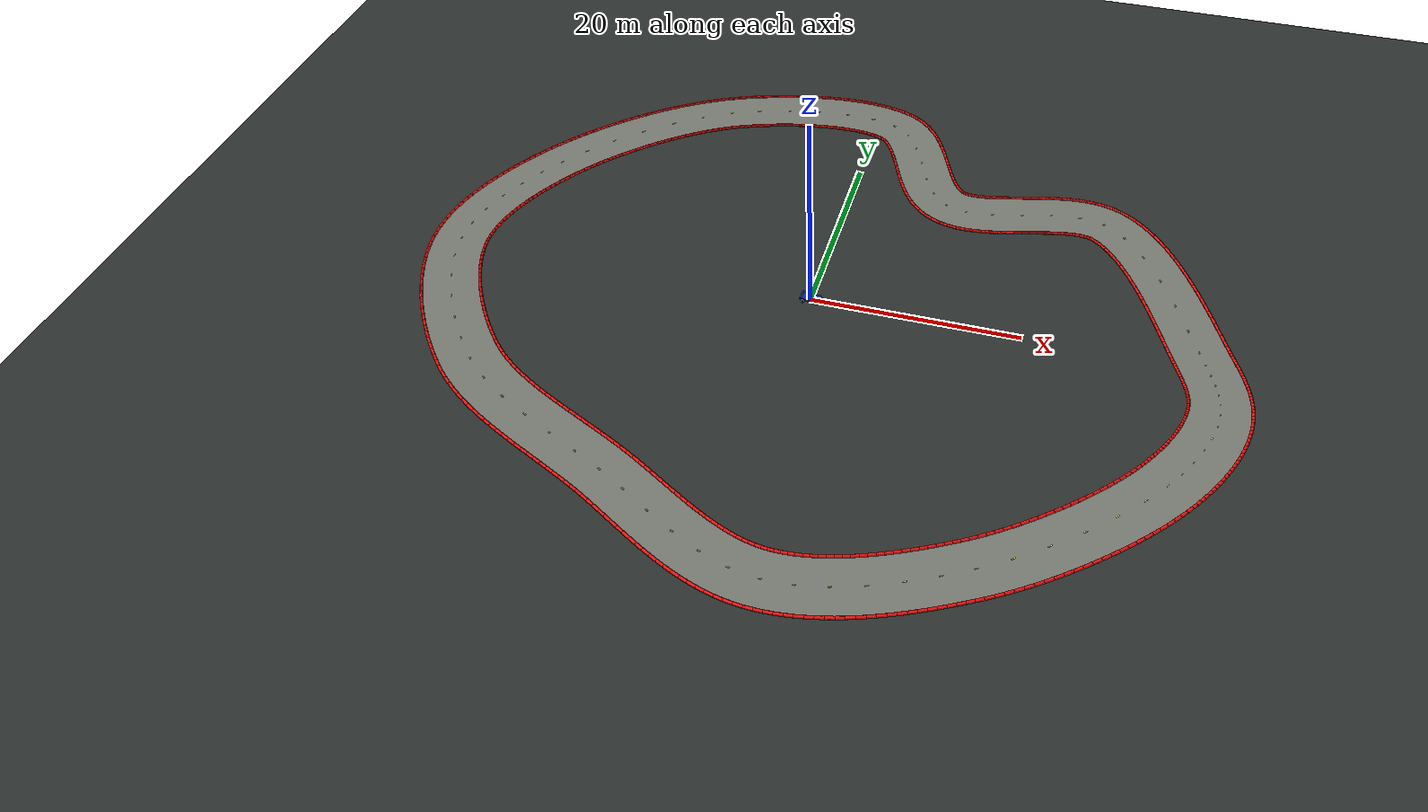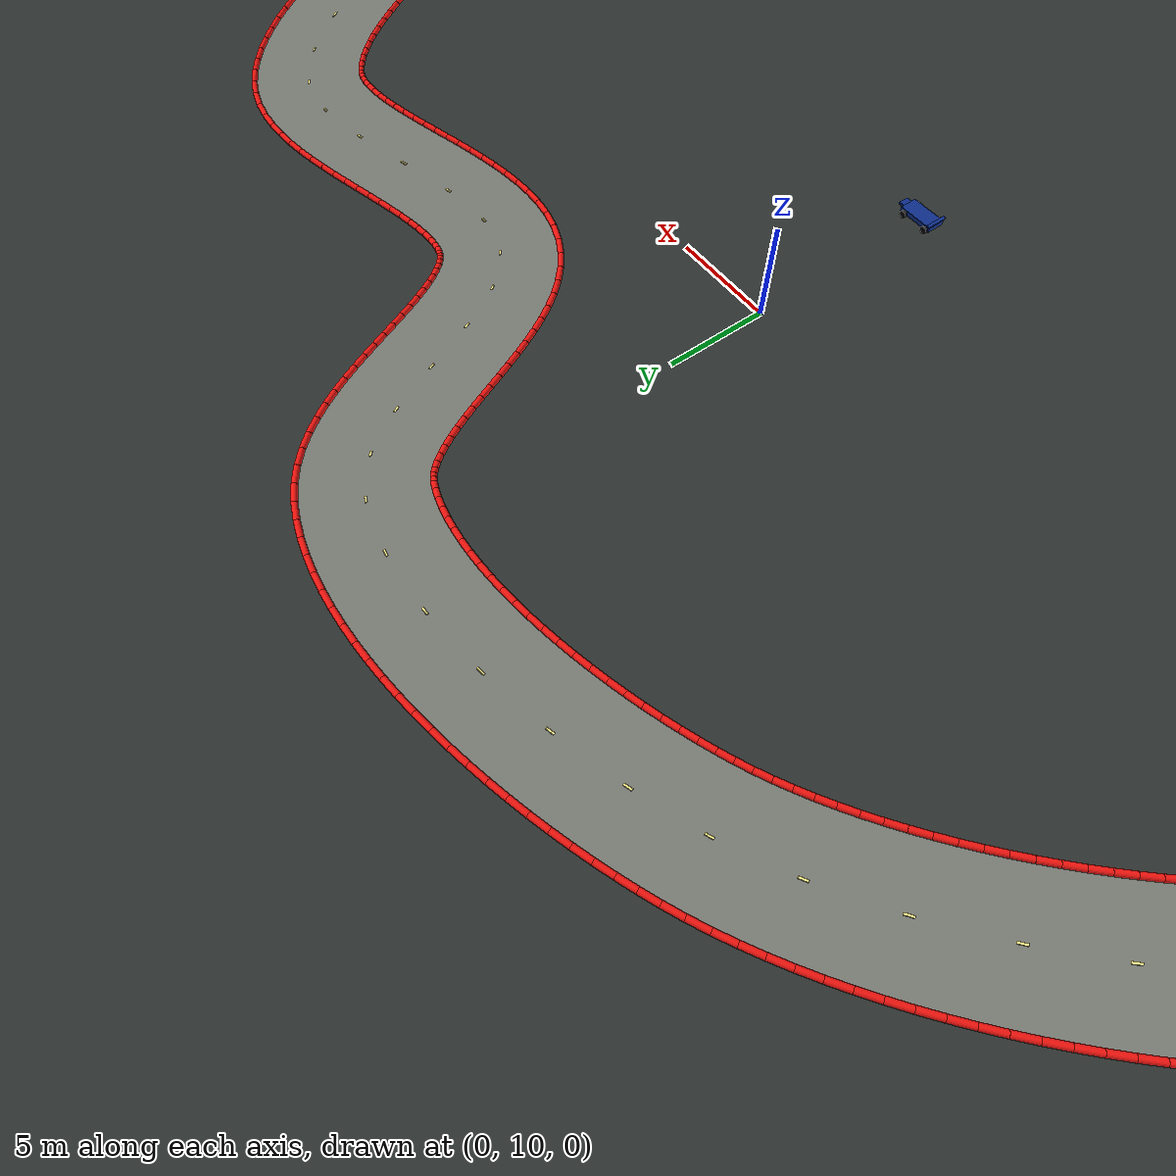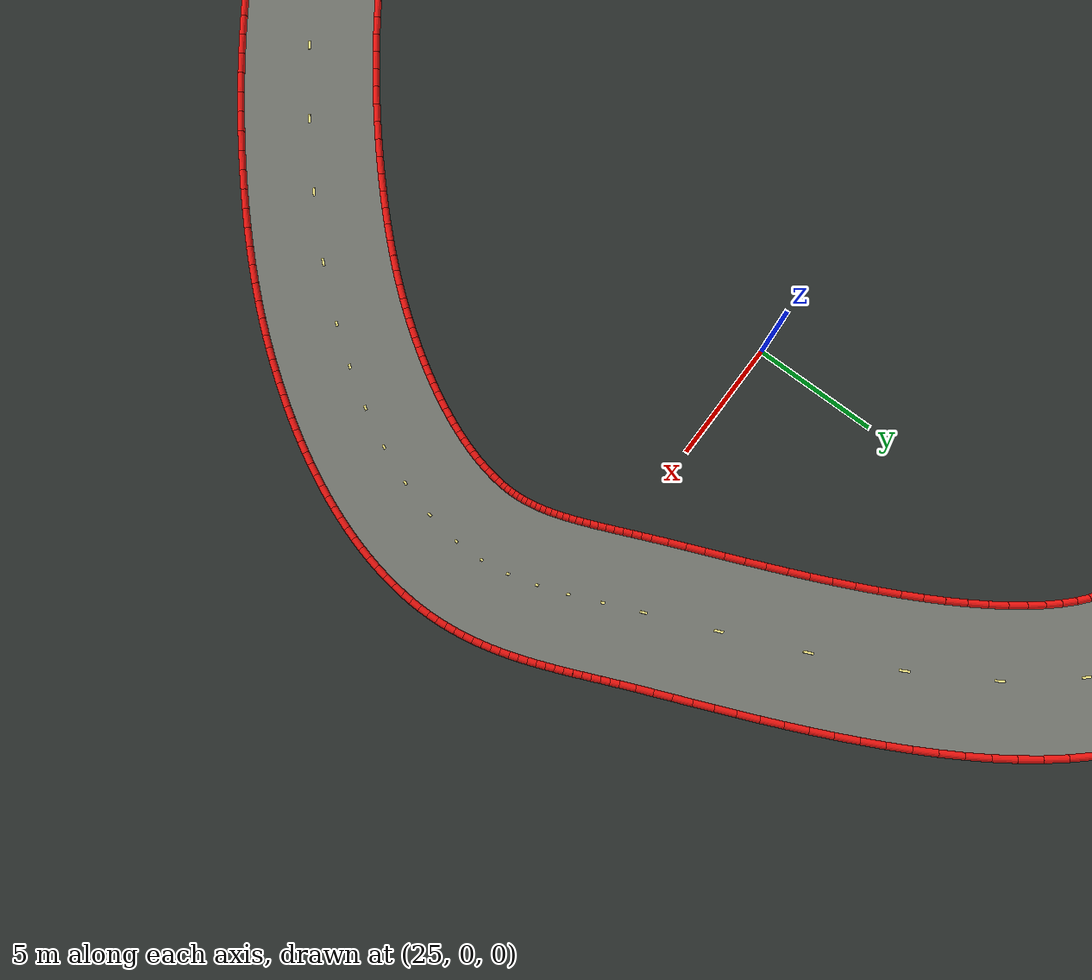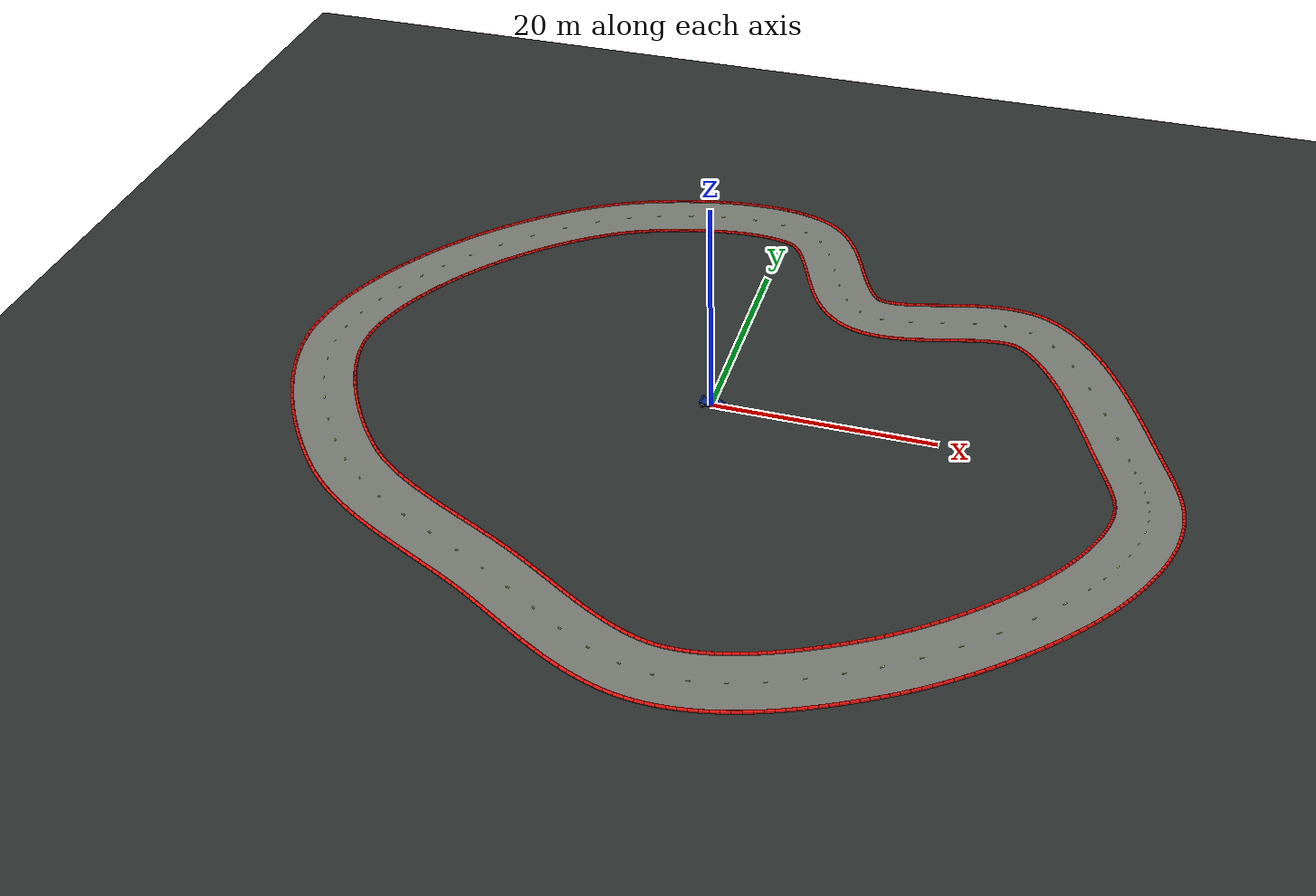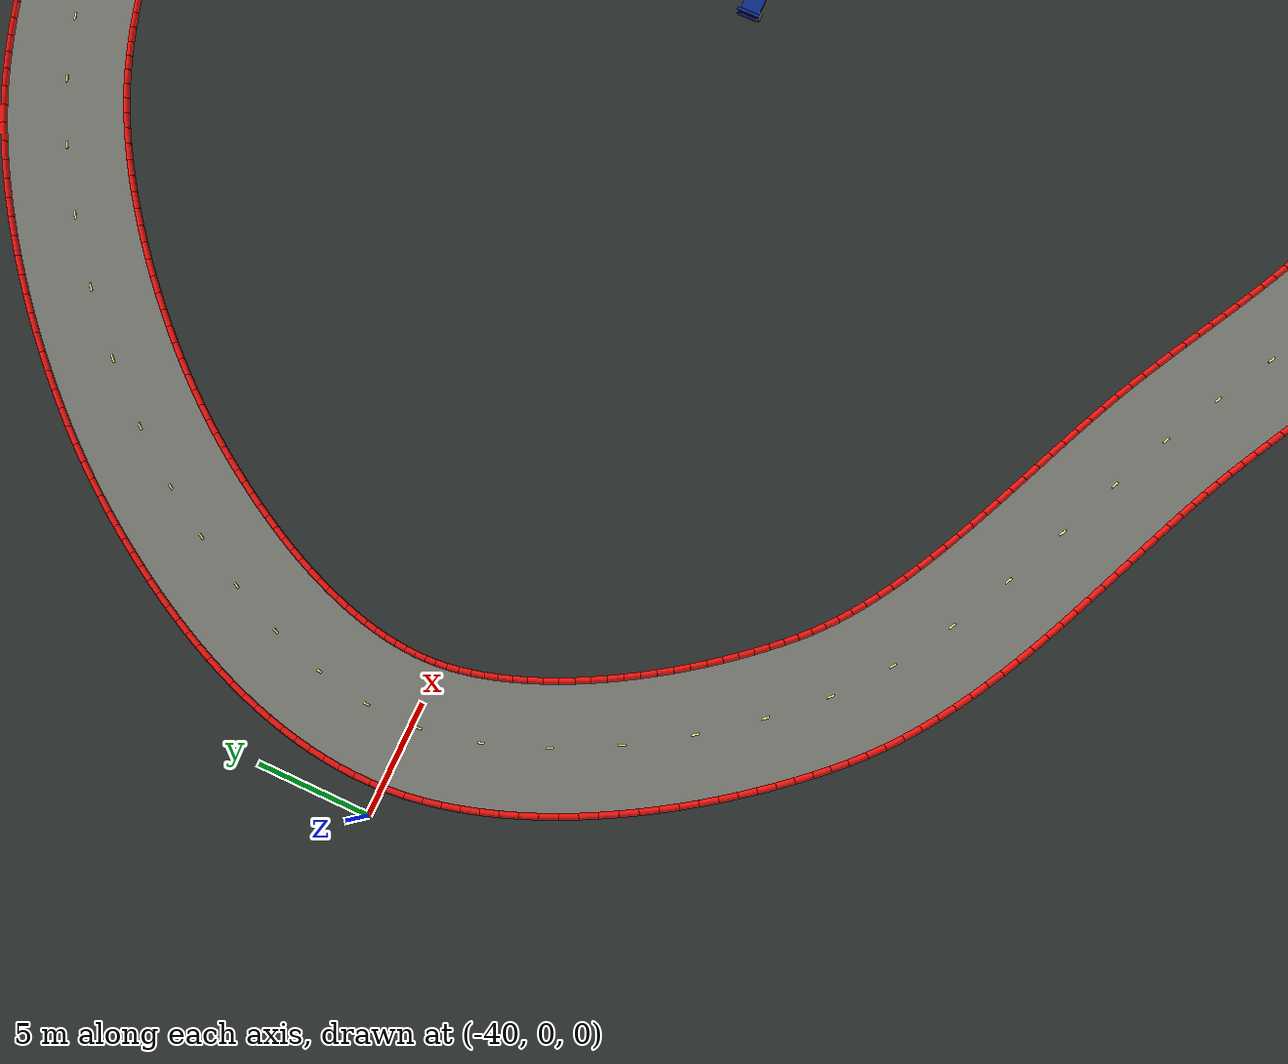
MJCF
<mujoco model="racesim_kartplex_world">
  <compiler angle="degree" autolimits="true"/>
  <option timestep="0.02" gravity="0 0 -9.81"/>
  <visual>
    <global offwidth="1280" offheight="960"/>
    <headlight ambient="0.35 0.35 0.35" diffuse="0.8 0.8 0.8"/>
  </visual>

  <include file="car.xml"/>
  <include file="kartplex_track.xml"/>

  <asset>
    <texture name="grid" type="2d" builtin="checker" width="512" height="512"
             rgb1="0.16 0.18 0.17" rgb2="0.20 0.22 0.21"/>
    <material name="ground" texture="grid" texrepeat="10 10" reflectance="0.05"/>
  </asset>

  <worldbody>
    <light name="sun" pos="0 0 30" dir="0 0 -1" diffuse="1.0 1.0 1.0" ambient="0.25 0.25 0.25"/>
    <geom name="ground" type="plane" size="80 80 0.1" material="ground"/>
    <camera name="topdown" pos="0 0 95" xyaxes="1 0 0 0 1 0" fovy="42"/>
    <camera name="follow" mode="trackcom" target="car" pos="-5 0 3" xyaxes="0 -1 0 0.5 0 0.866"/>
  </worldbody>
</mujoco>

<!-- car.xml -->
<mujoco model="simple_car">
  <default>
    <geom friction="1.2 0.02 0.001" density="600"/>
    <joint damping="0.1"/>
  </default>

  <asset>
    <material name="chassis_blue" rgba="0.05 0.18 0.55 1"/>
    <material name="wheel_dark" rgba="0.02 0.02 0.025 1"/>
  </asset>

  <worldbody>
    <body name="car" pos="0 0 0.28">
      <freejoint name="root"/>
      <geom name="chassis" type="box" size="0.9 0.45 0.12" material="chassis_blue"/>
      <geom name="nose" type="box" pos="0.75 0 0.02" size="0.45 0.25 0.06" material="chassis_blue"/>
      <geom name="rear_wing" type="box" pos="-0.85 0 0.22" size="0.08 0.55 0.04" material="chassis_blue"/>

      <body name="front_left_wheel" pos="0.65 0.48 -0.12">
        <joint name="front_left_spin" type="hinge" axis="0 1 0"/>
        <geom type="cylinder" size="0.18 0.08" euler="90 0 0" material="wheel_dark"/>
      </body>
      <body name="front_right_wheel" pos="0.65 -0.48 -0.12">
        <joint name="front_right_spin" type="hinge" axis="0 1 0"/>
        <geom type="cylinder" size="0.18 0.08" euler="90 0 0" material="wheel_dark"/>
      </body>
      <body name="rear_left_wheel" pos="-0.65 0.48 -0.12">
        <joint name="rear_left_spin" type="hinge" axis="0 1 0"/>
        <geom type="cylinder" size="0.18 0.08" euler="90 0 0" material="wheel_dark"/>
      </body>
      <body name="rear_right_wheel" pos="-0.65 -0.48 -0.12">
        <joint name="rear_right_spin" type="hinge" axis="0 1 0"/>
        <geom type="cylinder" size="0.18 0.08" euler="90 0 0" material="wheel_dark"/>
      </body>
    </body>
  </worldbody>
</mujoco>

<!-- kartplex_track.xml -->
<mujoco model="kartplex_track_visuals">
  <asset>
    <mesh name="track_surface_mesh" inertia="shell" vertex="33.48561 0.88630 0.02200 33.22842 1.47187 0.02200 32.95759 2.09919 0.02200 32.67474 2.75950 0.02200 32.37942 3.44901 0.02200 32.07143 4.16345 0.02200 31.75075 4.89825 0.02200 31.41752 5.64856 0.02200 31.07195 6.40939 0.02200 30.71438 7.17561 0.02200 30.34522 7.94193 0.02200 29.96503 8.70297 0.02200 29.57445 9.45326 0.02200 29.17432 10.18718 0.02200 28.76567 10.89903 0.02200 28.34977 11.58300 0.02200 27.92823 12.23317 0.02200 27.50309 12.84358 0.02200 27.07694 13.40823 0.02200 26.65308 13.92122 0.02200 26.23569 14.37695 0.02200 25.82995 14.77047 0.02200 25.44208 15.09806 0.02200 25.07904 15.35802 0.02200 24.76409 15.54337 0.02200 24.53082 15.64437 0.02200 24.26863 15.71749 0.02200 23.94050 15.77053 0.02200 23.54391 15.79646 0.02200 23.08237 15.79001 0.02200 22.56247 15.74882 0.02200 21.99181 15.67325 0.02200 21.37785 15.56574 0.02200 20.72739 15.43020 0.02200 20.04639 15.27147 0.02200 19.33998 15.09502 0.02200 18.61246 14.90668 0.02200 17.86734 14.71259 0.02200 17.10738 14.51908 0.02200 16.33450 14.33276 0.02200 15.54977 14.16059 0.02200 14.75331 14.01007 0.02200 13.94422 13.88963 0.02200 13.12066 13.80913 0.02200 12.28021 13.78063 0.02200 11.42096 13.81931 0.02200 10.54367 13.94405 0.02200 9.65541 14.17673 0.02200 8.78239 14.53425 0.02200 7.99934 14.99125 0.02200 7.30759 15.52560 0.02200 6.70422 16.11255 0.02200 6.17893 16.73357 0.02200 5.71895 17.37613 0.02200 5.31193 18.03215 0.02200 4.94710 18.69608 0.02200 4.61549 19.36357 0.02200 4.30974 20.03062 0.02200 4.02380 20.69314 0.02200 3.75267 21.34668 0.02200 3.49217 21.98638 0.02200 3.23886 22.60688 0.02200 2.99000 23.20237 0.02200 2.74358 23.76656 0.02200 2.49846 24.29275 0.02200 2.25457 24.77398 0.02200 2.01316 25.20325 0.02200 1.77707 25.57407 0.02200 1.55089 25.88138 0.02200 1.34052 26.12295 0.02200 1.15176 26.30111 0.02200 0.98728 26.42415 0.02200 0.80382 26.52378 0.02200 0.47033 26.66028 0.02200 0.05235 26.79748 0.02200 -0.41633 26.91677 0.02200 -0.93218 27.01522 0.02200 -1.49106 27.09076 0.02200 -2.08860 27.14211 0.02200 -2.72036 27.16858 0.02200 -3.38199 27.16999 0.02200 -4.06923 27.14657 0.02200 -4.77799 27.09881 0.02200 -5.50431 27.02744 0.02200 -6.24433 26.93336 0.02200 -6.99432 26.81759 0.02200 -7.75066 26.68125 0.02200 -8.50978 26.52556 0.02200 -9.26817 26.35177 0.02200 -10.02240 26.16122 0.02200 -10.76902 25.95528 0.02200 -11.50465 25.73539 0.02200 -12.22585 25.50301 0.02200 -12.92922 25.25970 0.02200 -13.61129 25.00706 0.02200 -14.26854 24.74679 0.02200 -14.89017 24.48389 0.02200 -15.51787 24.19571 0.02200 -16.14686 23.88011 0.02200 -16.78363 23.53468 0.02200 -17.42603 23.16093 0.02200 -18.07203 22.76046 0.02200 -18.71966 22.33493 0.02200 -19.36705 21.88605 0.02200 -20.01238 21.41555 0.02200 -20.65391 20.92520 0.02200 -21.28993 20.41677 0.02200 -21.91877 19.89208 0.02200 -22.53883 19.35294 0.02200 -23.14850 18.80119 0.02200 -23.74621 18.23868 0.02200 -24.33041 17.66727 0.02200 -24.89957 17.08887 0.02200 -25.45216 16.50539 0.02200 -25.98668 15.91876 0.02200 -26.50161 15.33098 0.02200 -26.99545 14.74408 0.02200 -27.46669 14.16013 0.02200 -27.91384 13.58129 0.02200 -28.33537 13.00980 0.02200 -28.73414 12.44167 0.02200 -29.06819 11.94569 0.02200 -29.40012 11.43717 0.02200 -29.72472 10.92296 0.02200 -30.04099 10.40376 0.02200 -30.34793 9.88032 0.02200 -30.64455 9.35338 0.02200 -30.92989 8.82372 0.02200 -31.20297 8.29212 0.02200 -31.46286 7.75938 0.02200 -31.70866 7.22632 0.02200 -31.93946 6.69379 0.02200 -32.15441 6.16263 0.02200 -32.35270 5.63372 0.02200 -32.53355 5.10793 0.02200 -32.69624 4.58615 0.02200 -32.84011 4.06925 0.02200 -32.96456 3.55811 0.02200 -33.06906 3.05356 0.02200 -33.15318 2.55640 0.02200 -33.21654 2.06735 0.02200 -33.25885 1.58703 0.02200 -33.27989 1.11596 0.02200 -33.27948 0.65449 0.02200 -33.25764 0.20486 0.02200 -33.20831 -0.28496 0.02200 -33.13109 -0.79163 0.02200 -33.02557 -1.31764 0.02200 -32.89203 -1.86067 0.02200 -32.73100 -2.41835 0.02200 -32.54321 -2.98837 0.02200 -32.32960 -3.56845 0.02200 -32.09123 -4.15642 0.02200 -31.82926 -4.75014 0.02200 -31.54495 -5.34758 0.02200 -31.23963 -5.94676 0.02200 -30.91468 -6.54576 0.02200 -30.57151 -7.14272 0.02200 -30.21161 -7.73582 0.02200 -29.83644 -8.32329 0.02200 -29.44755 -8.90340 0.02200 -29.04646 -9.47442 0.02200 -28.63476 -10.03467 0.02200 -28.21405 -10.58249 0.02200 -27.78596 -11.11621 0.02200 -27.35217 -11.63419 0.02200 -26.91439 -12.13477 0.02200 -26.47438 -12.61632 0.02200 -26.04433 -13.06665 0.02200 -25.60328 -13.49826 0.02200 -25.14593 -13.90871 0.02200 -24.66153 -14.31010 0.02200 -24.15107 -14.70272 0.02200 -23.61571 -15.08686 0.02200 -23.05677 -15.46284 0.02200 -22.47567 -15.83102 0.02200 -21.87394 -16.19180 0.02200 -21.25316 -16.54566 0.02200 -20.61496 -16.89315 0.02200 -19.96099 -17.23489 0.02200 -19.29294 -17.57155 0.02200 -18.61247 -17.90388 0.02200 -17.92126 -18.23266 0.02200 -17.22096 -18.55876 0.02200 -16.51322 -18.88309 0.02200 -15.79964 -19.20659 0.02200 -15.08184 -19.53029 0.02200 -14.36138 -19.85522 0.02200 -13.63980 -20.18251 0.02200 -12.91861 -20.51331 0.02200 -12.19932 -20.84885 0.02200 -11.48338 -21.19039 0.02200 -10.77058 -21.54012 0.02200 -10.07527 -21.89407 0.02200 -9.38286 -22.25961 0.02200 -8.69681 -22.63238 0.02200 -8.01677 -23.01003 0.02200 -7.34249 -23.39024 0.02200 -6.67378 -23.77071 0.02200 -6.01055 -24.14916 0.02200 -5.35282 -24.52332 0.02200 -4.70064 -24.89097 0.02200 -4.05417 -25.24986 0.02200 -3.41366 -25.59780 0.02200 -2.77943 -25.93262 0.02200 -2.15187 -26.25220 0.02200 -1.53146 -26.55446 0.02200 -0.91877 -26.83742 0.02200 -0.31441 -27.09917 0.02200 0.28095 -27.33794 0.02200 0.86663 -27.55210 0.02200 1.44195 -27.74021 0.02200 2.00630 -27.90102 0.02200 2.55923 -28.03352 0.02200 3.10050 -28.13690 0.02200 3.63020 -28.21056 0.02200 4.15901 -28.25460 0.02200 4.69237 -28.27162 0.02200 5.24466 -28.26560 0.02200 5.80792 -28.23648 0.02200 6.38152 -28.18468 0.02200 6.96469 -28.11069 0.02200 7.55661 -28.01508 0.02200 8.15639 -27.89850 0.02200 8.76311 -27.76166 0.02200 9.37581 -27.60537 0.02200 9.99356 -27.43045 0.02200 10.61539 -27.23783 0.02200 11.24038 -27.02844 0.02200 11.86760 -26.80329 0.02200 12.49613 -26.56340 0.02200 13.12510 -26.30982 0.02200 13.75362 -26.04363 0.02200 14.38085 -25.76593 0.02200 15.00595 -25.47782 0.02200 15.62813 -25.18043 0.02200 16.24659 -24.87489 0.02200 16.86055 -24.56234 0.02200 17.46927 -24.24392 0.02200 18.07202 -23.92079 0.02200 18.65938 -23.59891 0.02200 19.26107 -23.25684 0.02200 19.86381 -22.89675 0.02200 20.47436 -22.51520 0.02200 21.09065 -22.11373 0.02200 21.71067 -21.69390 0.02200 22.33249 -21.25725 0.02200 22.95424 -20.80535 0.02200 23.57408 -20.33975 0.02200 24.19020 -19.86202 0.02200 24.80081 -19.37374 0.02200 25.40418 -18.87648 0.02200 25.99854 -18.37182 0.02200 26.58216 -17.86139 0.02200 27.15331 -17.34679 0.02200 27.71027 -16.82968 0.02200 28.25129 -16.31172 0.02200 28.77465 -15.79464 0.02200 29.27859 -15.28020 0.02200 29.76134 -14.77021 0.02200 30.22112 -14.26659 0.02200 30.65613 -13.77134 0.02200 31.06451 -13.28659 0.02200 31.44442 -12.81467 0.02200 31.79948 -12.35069 0.02200 32.04414 -12.01718 0.02200 32.28680 -11.67620 0.02200 32.52210 -11.33484 0.02200 32.74971 -10.99346 0.02200 32.96927 -10.65243 0.02200 33.18047 -10.31212 0.02200 33.38297 -9.97293 0.02200 33.57646 -9.63526 0.02200 33.76064 -9.29952 0.02200 33.93521 -8.96614 0.02200 34.09988 -8.63555 0.02200 34.25440 -8.30821 0.02200 34.39851 -7.98457 0.02200 34.53200 -7.66512 0.02200 34.65466 -7.35034 0.02200 34.76632 -7.04072 0.02200 34.86685 -6.73676 0.02200 34.95614 -6.43897 0.02200 35.03416 -6.14786 0.02200 35.10088 -5.86390 0.02200 35.15637 -5.58757 0.02200 35.20071 -5.31931 0.02200 35.23407 -5.05951 0.02200 35.25683 -4.80632 0.02200 35.26703 -4.60755 0.02200 35.26971 -4.41377 0.02200 35.26519 -4.22477 0.02200 35.25377 -4.03879 0.02200 35.23557 -3.85408 0.02200 35.21060 -3.66897 0.02200 35.17875 -3.48187 0.02200 35.13981 -3.29134 0.02200 35.09355 -3.09609 0.02200 35.03972 -2.89502 0.02200 34.97808 -2.68716 0.02200 34.90846 -2.47169 0.02200 34.83075 -2.24795 0.02200 34.74489 -2.01537 0.02200 34.65096 -1.77346 0.02200 34.54907 -1.52180 0.02200 34.43945 -1.26002 0.02200 34.32239 -0.98778 0.02200 34.19824 -0.70475 0.02200 34.06741 -0.41063 0.02200 33.93036 -0.10510 0.02200 33.78758 0.21217 0.02200 33.63961 0.54149 0.02200 38.51439 3.11370 0.02200 38.27107 3.66771 0.02200 38.01021 4.27198 0.02200 37.73048 4.92504 0.02200 37.43264 5.62040 0.02200 37.11720 6.35210 0.02200 36.78447 7.11447 0.02200 36.43465 7.90209 0.02200 36.06781 8.70969 0.02200 35.68394 9.53219 0.02200 35.28290 10.36459 0.02200 34.86449 11.20203 0.02200 34.42832 12.03975 0.02200 33.97389 12.87309 0.02200 33.50048 13.69752 0.02200 33.00711 14.50859 0.02200 32.49249 15.30197 0.02200 31.95488 16.07337 0.02200 31.39199 16.81856 0.02200 30.80084 17.53316 0.02200 30.17755 18.21254 0.02200 29.51726 18.85138 0.02200 28.81404 19.44316 0.02200 28.06123 19.97933 0.02200 27.23591 20.45663 0.02200 26.37189 20.82708 0.02200 25.47086 21.08449 0.02200 24.57600 21.23369 0.02200 23.69604 21.29436 0.02200 22.83365 21.28438 0.02200 21.98846 21.21878 0.02200 21.15904 21.10983 0.02200 20.34414 20.96772 0.02200 19.54316 20.80119 0.02200 18.75630 20.61803 0.02200 17.98466 20.42541 0.02200 17.23013 20.23014 0.02200 16.49537 20.03872 0.02200 15.78385 19.85746 0.02200 15.09981 19.69239 0.02200 14.44839 19.54919 0.02200 13.83567 19.43298 0.02200 13.26873 19.34799 0.02200 12.75562 19.29700 0.02200 12.30494 19.28058 0.02200 11.92481 19.29618 0.02200 11.62064 19.33758 0.02200 11.39159 19.39552 0.02200 11.21761 19.46575 0.02200 11.07931 19.54798 0.02200 10.91829 19.67444 0.02200 10.73114 19.85874 0.02200 10.52185 20.10833 0.02200 10.29682 20.42459 0.02200 10.06209 20.80451 0.02200 9.82210 21.24253 0.02200 9.57947 21.73187 0.02200 9.33524 22.26541 0.02200 9.08912 22.83615 0.02200 8.83979 23.43741 0.02200 8.58509 24.06295 0.02200 8.32212 24.70698 0.02200 8.04730 25.36424 0.02200 7.75630 26.02988 0.02200 7.44393 26.69949 0.02200 7.10392 27.36893 0.02200 6.72871 28.03407 0.02200 6.30909 28.69028 0.02200 5.83418 29.33152 0.02200 5.29171 29.94892 0.02200 4.66957 30.52900 0.02200 3.95875 31.05237 0.02200 3.19618 31.47622 0.02200 2.38912 31.81472 0.02200 1.59346 32.07716 0.02200 0.78115 32.28483 0.02200 -0.04566 32.44330 0.02200 -0.88540 32.55731 0.02200 -1.73675 32.63084 0.02200 -2.59844 32.66722 0.02200 -3.46911 32.66930 0.02200 -4.34733 32.63953 0.02200 -5.23148 32.58008 0.02200 -6.11983 32.49289 0.02200 -7.01053 32.37973 0.02200 -7.90160 32.24224 0.02200 -8.79098 32.08197 0.02200 -9.67652 31.90038 0.02200 -10.55603 31.69887 0.02200 -11.42725 31.47878 0.02200 -12.28791 31.24140 0.02200 -13.13571 30.98797 0.02200 -13.96837 30.71968 0.02200 -14.78360 30.43766 0.02200 -15.57916 30.14296 0.02200 -16.35286 29.83655 0.02200 -17.10983 29.51611 0.02200 -17.89906 29.15353 0.02200 -18.69143 28.75609 0.02200 -19.47789 28.32957 0.02200 -20.25798 27.87581 0.02200 -21.03116 27.39657 0.02200 -21.79681 26.89357 0.02200 -22.55422 26.36846 0.02200 -23.30261 25.82286 0.02200 -24.04116 25.25839 0.02200 -24.76897 24.67661 0.02200 -25.48514 24.07909 0.02200 -26.18868 23.46738 0.02200 -26.87863 22.84299 0.02200 -27.55395 22.20744 0.02200 -28.21361 21.56223 0.02200 -28.85657 20.90883 0.02200 -29.48177 20.24869 0.02200 -30.08812 19.58321 0.02200 -30.67455 18.91379 0.02200 -31.24000 18.24177 0.02200 -31.78336 17.56841 0.02200 -32.30357 16.89493 0.02200 -32.79955 16.22245 0.02200 -33.26586 15.55833 0.02200 -33.65193 14.98532 0.02200 -34.02855 14.40831 0.02200 -34.39892 13.82156 0.02200 -34.76201 13.22546 0.02200 -35.11680 12.62036 0.02200 -35.46227 12.00661 0.02200 -35.79735 11.38453 0.02200 -36.12099 10.75444 0.02200 -36.43211 10.11663 0.02200 -36.72959 9.47137 0.02200 -37.01231 8.81893 0.02200 -37.27910 8.15954 0.02200 -37.52875 7.49343 0.02200 -37.76003 6.82081 0.02200 -37.97162 6.14191 0.02200 -38.16217 5.45693 0.02200 -38.33026 4.76611 0.02200 -38.47438 4.06970 0.02200 -38.59297 3.36800 0.02200 -38.68436 2.66140 0.02200 -38.74684 1.95035 0.02200 -38.77859 1.23544 0.02200 -38.77777 0.51742 0.02200 -38.74236 -0.20486 0.02200 -38.66495 -0.97424 0.02200 -38.54768 -1.74586 0.02200 -38.39377 -2.51450 0.02200 -38.20579 -3.27980 0.02200 -37.98607 -4.04139 0.02200 -37.73668 -4.79888 0.02200 -37.45954 -5.55183 0.02200 -37.15643 -6.29971 0.02200 -36.82902 -7.04194 0.02200 -36.47890 -7.77784 0.02200 -36.10756 -8.50669 0.02200 -35.71647 -9.22769 0.02200 -35.30705 -9.93998 0.02200 -34.88067 -10.64268 0.02200 -34.43868 -11.33484 0.02200 -33.98239 -12.01549 0.02200 -33.51310 -12.68364 0.02200 -33.03207 -13.33825 0.02200 -32.54054 -13.97829 0.02200 -32.03971 -14.60271 0.02200 -31.53074 -15.21043 0.02200 -31.01477 -15.80040 0.02200 -30.49286 -16.37155 0.02200 -29.95567 -16.93335 0.02200 -29.36386 -17.51173 0.02200 -28.73860 -18.07317 0.02200 -28.09384 -18.60769 0.02200 -27.43182 -19.11709 0.02200 -26.75461 -19.60320 0.02200 -26.06411 -20.06783 0.02200 -25.36212 -20.51273 0.02200 -24.65034 -20.93960 0.02200 -23.93041 -21.35007 0.02200 -23.20392 -21.74571 0.02200 -22.47243 -22.12802 0.02200 -21.73749 -22.49843 0.02200 -21.00066 -22.85832 0.02200 -20.26349 -23.20900 0.02200 -19.52754 -23.55173 0.02200 -18.79438 -23.88771 0.02200 -18.06564 -24.21811 0.02200 -17.34293 -24.54401 0.02200 -16.62790 -24.86650 0.02200 -15.92224 -25.18655 0.02200 -15.22765 -25.50514 0.02200 -14.54587 -25.82315 0.02200 -13.87864 -26.14142 0.02200 -13.22942 -26.45988 0.02200 -12.60685 -26.77681 0.02200 -11.97985 -27.10787 0.02200 -11.34501 -27.45286 0.02200 -10.70269 -27.80960 0.02200 -10.05317 -28.17587 0.02200 -9.39665 -28.54941 0.02200 -8.73324 -28.92796 0.02200 -8.06297 -29.30925 0.02200 -7.38579 -29.69096 0.02200 -6.70157 -30.07078 0.02200 -6.01009 -30.44636 0.02200 -5.31105 -30.81533 0.02200 -4.60409 -31.17527 0.02200 -3.88873 -31.52370 0.02200 -3.16445 -31.85807 0.02200 -2.43066 -32.17573 0.02200 -1.68671 -32.47392 0.02200 -0.93193 -32.74971 0.02200 -0.16568 -33.00001 0.02200 0.61263 -33.22152 0.02200 1.40343 -33.41070 0.02200 2.20693 -33.56382 0.02200 3.02301 -33.67694 0.02200 3.84099 -33.74540 0.02200 4.63298 -33.77130 0.02200 5.41600 -33.76293 0.02200 6.19673 -33.72272 0.02200 6.97456 -33.65261 0.02200 7.74897 -33.55449 0.02200 8.51955 -33.43013 0.02200 9.28590 -33.28127 0.02200 10.04770 -33.10954 0.02200 10.80463 -32.91653 0.02200 11.55636 -32.70375 0.02200 12.30260 -32.47265 0.02200 13.04301 -32.22465 0.02200 13.77725 -31.96113 0.02200 14.50498 -31.68342 0.02200 15.22582 -31.39283 0.02200 15.93937 -31.09066 0.02200 16.64523 -30.77817 0.02200 17.34297 -30.45661 0.02200 18.03212 -30.12723 0.02200 18.71221 -29.79126 0.02200 19.38276 -29.44992 0.02200 20.04325 -29.10444 0.02200 20.69316 -28.75604 0.02200 21.34062 -28.40109 0.02200 22.03093 -28.00846 0.02200 22.73160 -27.58991 0.02200 23.43282 -27.15174 0.02200 24.13361 -26.69525 0.02200 24.83295 -26.22174 0.02200 25.52973 -25.73248 0.02200 26.22277 -25.22878 0.02200 26.91088 -24.71191 0.02200 27.59283 -24.18315 0.02200 28.26734 -23.64377 0.02200 28.93315 -23.09505 0.02200 29.58895 -22.53823 0.02200 30.23344 -21.97455 0.02200 30.86531 -21.40524 0.02200 31.48325 -20.83150 0.02200 32.08595 -20.25449 0.02200 32.67210 -19.67535 0.02200 33.24042 -19.09515 0.02200 33.78964 -18.51492 0.02200 34.31849 -17.93559 0.02200 34.82575 -17.35802 0.02200 35.31021 -16.78289 0.02200 35.77069 -16.21075 0.02200 36.20052 -15.64931 0.02200 36.50190 -15.23872 0.02200 36.79168 -14.83152 0.02200 37.07457 -14.42112 0.02200 37.35022 -14.00765 0.02200 37.61831 -13.59121 0.02200 37.87850 -13.17192 0.02200 38.13045 -12.74987 0.02200 38.37381 -12.32514 0.02200 38.60821 -11.89780 0.02200 38.83328 -11.46792 0.02200 39.04862 -11.03554 0.02200 39.25385 -10.60070 0.02200 39.44853 -10.16341 0.02200 39.63222 -9.72369 0.02200 39.80446 -9.28154 0.02200 39.96474 -8.83694 0.02200 40.11253 -8.38988 0.02200 40.24726 -7.94035 0.02200 40.36831 -7.48831 0.02200 40.47502 -7.03378 0.02200 40.56668 -6.57676 0.02200 40.64251 -6.11730 0.02200 40.70169 -5.65549 0.02200 40.74317 -5.19368 0.02200 40.76411 -4.78676 0.02200 40.76964 -4.38613 0.02200 40.76021 -3.99073 0.02200 40.73632 -3.60105 0.02200 40.69861 -3.21756 0.02200 40.64787 -2.84066 0.02200 40.58499 -2.47067 0.02200 40.51095 -2.10774 0.02200 40.42676 -1.75190 0.02200 40.33347 -1.40299 0.02200 40.23209 -1.06068 0.02200 40.12358 -0.72453 0.02200 40.00883 -0.39392 0.02200 39.88866 -0.06816 0.02200 39.76381 0.25354 0.02200 39.63492 0.57204 0.02200 39.50255 0.88825 0.02200 39.36720 1.20308 0.02200 39.22930 1.51749 0.02200 39.08922 1.83245 0.02200 38.94728 2.14891 0.02200 38.80376 2.46782 0.02200 38.65893 2.79014 0.02200" face="0 313 1 0 312 313 1 314 2 1 313 314 2 315 3 2 314 315 3 316 4 3 315 316 4 317 5 4 316 317 5 318 6 5 317 318 6 319 7 6 318 319 7 320 8 7 319 320 8 321 9 8 320 321 9 322 10 9 321 322 10 323 11 10 322 323 11 324 12 11 323 324 12 325 13 12 324 325 13 326 14 13 325 326 14 327 15 14 326 327 15 328 16 15 327 328 16 329 17 16 328 329 17 330 18 17 329 330 18 331 19 18 330 331 19 332 20 19 331 332 20 333 21 20 332 333 21 334 22 21 333 334 22 335 23 22 334 335 23 336 24 23 335 336 24 337 25 24 336 337 25 338 26 25 337 338 26 339 27 26 338 339 27 340 28 27 339 340 28 341 29 28 340 341 29 342 30 29 341 342 30 343 31 30 342 343 31 344 32 31 343 344 32 345 33 32 344 345 33 346 34 33 345 346 34 347 35 34 346 347 35 348 36 35 347 348 36 349 37 36 348 349 37 350 38 37 349 350 38 351 39 38 350 351 39 352 40 39 351 352 40 353 41 40 352 353 41 354 42 41 353 354 42 355 43 42 354 355 43 356 44 43 355 356 44 357 45 44 356 357 45 358 46 45 357 358 46 359 47 46 358 359 47 360 48 47 359 360 48 361 49 48 360 361 49 362 50 49 361 362 50 363 51 50 362 363 51 364 52 51 363 364 52 365 53 52 364 365 53 366 54 53 365 366 54 367 55 54 366 367 55 368 56 55 367 368 56 369 57 56 368 369 57 370 58 57 369 370 58 371 59 58 370 371 59 372 60 59 371 372 60 373 61 60 372 373 61 374 62 61 373 374 62 375 63 62 374 375 63 376 64 63 375 376 64 377 65 64 376 377 65 378 66 65 377 378 66 379 67 66 378 379 67 380 68 67 379 380 68 381 69 68 380 381 69 382 70 69 381 382 70 383 71 70 382 383 71 384 72 71 383 384 72 385 73 72 384 385 73 386 74 73 385 386 74 387 75 74 386 387 75 388 76 75 387 388 76 389 77 76 388 389 77 390 78 77 389 390 78 391 79 78 390 391 79 392 80 79 391 392 80 393 81 80 392 393 81 394 82 81 393 394 82 395 83 82 394 395 83 396 84 83 395 396 84 397 85 84 396 397 85 398 86 85 397 398 86 399 87 86 398 399 87 400 88 87 399 400 88 401 89 88 400 401 89 402 90 89 401 402 90 403 91 90 402 403 91 404 92 91 403 404 92 405 93 92 404 405 93 406 94 93 405 406 94 407 95 94 406 407 95 408 96 95 407 408 96 409 97 96 408 409 97 410 98 97 409 410 98 411 99 98 410 411 99 412 100 99 411 412 100 413 101 100 412 413 101 414 102 101 413 414 102 415 103 102 414 415 103 416 104 103 415 416 104 417 105 104 416 417 105 418 106 105 417 418 106 419 107 106 418 419 107 420 108 107 419 420 108 421 109 108 420 421 109 422 110 109 421 422 110 423 111 110 422 423 111 424 112 111 423 424 112 425 113 112 424 425 113 426 114 113 425 426 114 427 115 114 426 427 115 428 116 115 427 428 116 429 117 116 428 429 117 430 118 117 429 430 118 431 119 118 430 431 119 432 120 119 431 432 120 433 121 120 432 433 121 434 122 121 433 434 122 435 123 122 434 435 123 436 124 123 435 436 124 437 125 124 436 437 125 438 126 125 437 438 126 439 127 126 438 439 127 440 128 127 439 440 128 441 129 128 440 441 129 442 130 129 441 442 130 443 131 130 442 443 131 444 132 131 443 444 132 445 133 132 444 445 133 446 134 133 445 446 134 447 135 134 446 447 135 448 136 135 447 448 136 449 137 136 448 449 137 450 138 137 449 450 138 451 139 138 450 451 139 452 140 139 451 452 140 453 141 140 452 453 141 454 142 141 453 454 142 455 143 142 454 455 143 456 144 143 455 456 144 457 145 144 456 457 145 458 146 145 457 458 146 459 147 146 458 459 147 460 148 147 459 460 148 461 149 148 460 461 149 462 150 149 461 462 150 463 151 150 462 463 151 464 152 151 463 464 152 465 153 152 464 465 153 466 154 153 465 466 154 467 155 154 466 467 155 468 156 155 467 468 156 469 157 156 468 469 157 470 158 157 469 470 158 471 159 158 470 471 159 472 160 159 471 472 160 473 161 160 472 473 161 474 162 161 473 474 162 475 163 162 474 475 163 476 164 163 475 476 164 477 165 164 476 477 165 478 166 165 477 478 166 479 167 166 478 479 167 480 168 167 479 480 168 481 169 168 480 481 169 482 170 169 481 482 170 483 171 170 482 483 171 484 172 171 483 484 172 485 173 172 484 485 173 486 174 173 485 486 174 487 175 174 486 487 175 488 176 175 487 488 176 489 177 176 488 489 177 490 178 177 489 490 178 491 179 178 490 491 179 492 180 179 491 492 180 493 181 180 492 493 181 494 182 181 493 494 182 495 183 182 494 495 183 496 184 183 495 496 184 497 185 184 496 497 185 498 186 185 497 498 186 499 187 186 498 499 187 500 188 187 499 500 188 501 189 188 500 501 189 502 190 189 501 502 190 503 191 190 502 503 191 504 192 191 503 504 192 505 193 192 504 505 193 506 194 193 505 506 194 507 195 194 506 507 195 508 196 195 507 508 196 509 197 196 508 509 197 510 198 197 509 510 198 511 199 198 510 511 199 512 200 199 511 512 200 513 201 200 512 513 201 514 202 201 513 514 202 515 203 202 514 515 203 516 204 203 515 516 204 517 205 204 516 517 205 518 206 205 517 518 206 519 207 206 518 519 207 520 208 207 519 520 208 521 209 208 520 521 209 522 210 209 521 522 210 523 211 210 522 523 211 524 212 211 523 524 212 525 213 212 524 525 213 526 214 213 525 526 214 527 215 214 526 527 215 528 216 215 527 528 216 529 217 216 528 529 217 530 218 217 529 530 218 531 219 218 530 531 219 532 220 219 531 532 220 533 221 220 532 533 221 534 222 221 533 534 222 535 223 222 534 535 223 536 224 223 535 536 224 537 225 224 536 537 225 538 226 225 537 538 226 539 227 226 538 539 227 540 228 227 539 540 228 541 229 228 540 541 229 542 230 229 541 542 230 543 231 230 542 543 231 544 232 231 543 544 232 545 233 232 544 545 233 546 234 233 545 546 234 547 235 234 546 547 235 548 236 235 547 548 236 549 237 236 548 549 237 550 238 237 549 550 238 551 239 238 550 551 239 552 240 239 551 552 240 553 241 240 552 553 241 554 242 241 553 554 242 555 243 242 554 555 243 556 244 243 555 556 244 557 245 244 556 557 245 558 246 245 557 558 246 559 247 246 558 559 247 560 248 247 559 560 248 561 249 248 560 561 249 562 250 249 561 562 250 563 251 250 562 563 251 564 252 251 563 564 252 565 253 252 564 565 253 566 254 253 565 566 254 567 255 254 566 567 255 568 256 255 567 568 256 569 257 256 568 569 257 570 258 257 569 570 258 571 259 258 570 571 259 572 260 259 571 572 260 573 261 260 572 573 261 574 262 261 573 574 262 575 263 262 574 575 263 576 264 263 575 576 264 577 265 264 576 577 265 578 266 265 577 578 266 579 267 266 578 579 267 580 268 267 579 580 268 581 269 268 580 581 269 582 270 269 581 582 270 583 271 270 582 583 271 584 272 271 583 584 272 585 273 272 584 585 273 586 274 273 585 586 274 587 275 274 586 587 275 588 276 275 587 588 276 589 277 276 588 589 277 590 278 277 589 590 278 591 279 278 590 591 279 592 280 279 591 592 280 593 281 280 592 593 281 594 282 281 593 594 282 595 283 282 594 595 283 596 284 283 595 596 284 597 285 284 596 597 285 598 286 285 597 598 286 599 287 286 598 599 287 600 288 287 599 600 288 601 289 288 600 601 289 602 290 289 601 602 290 603 291 290 602 603 291 604 292 291 603 604 292 605 293 292 604 605 293 606 294 293 605 606 294 607 295 294 606 607 295 608 296 295 607 608 296 609 297 296 608 609 297 610 298 297 609 610 298 611 299 298 610 611 299 612 300 299 611 612 300 613 301 300 612 613 301 614 302 301 613 614 302 615 303 302 614 615 303 616 304 303 615 616 304 617 305 304 616 617 305 618 306 305 617 618 306 619 307 306 618 619 307 620 308 307 619 620 308 621 309 308 620 621 309 622 310 309 621 622 310 623 311 310 622 623 311 312 0 311 623 312"/>
    <material name="track_asphalt" rgba="0.48 0.49 0.46 1" emission="0.08"/>
    <material name="track_boundary" rgba="0.95 0.08 0.06 1" emission="0.05"/>
    <material name="track_centerline" rgba="1.0 0.95 0.55 1" emission="0.15"/>
  </asset>
  <worldbody>
    <geom name="track_surface" type="mesh" mesh="track_surface_mesh" material="track_asphalt" contype="0" conaffinity="0"/>
    <geom name="track_left_boundary_000" type="capsule" fromto="33.48561 0.88630 0.09 33.22842 1.47187 0.09" size="0.14" material="track_boundary" contype="0" conaffinity="0"/>
    <geom name="track_left_boundary_001" type="capsule" fromto="33.22842 1.47187 0.09 32.95759 2.09919 0.09" size="0.14" material="track_boundary" contype="0" conaffinity="0"/>
    <geom name="track_left_boundary_002" type="capsule" fromto="32.95759 2.09919 0.09 32.67474 2.75950 0.09" size="0.14" material="track_boundary" contype="0" conaffinity="0"/>
    <geom name="track_left_boundary_003" type="capsule" fromto="32.67474 2.75950 0.09 32.37942 3.44901 0.09" size="0.14" material="track_boundary" contype="0" conaffinity="0"/>
    <geom name="track_left_boundary_004" type="capsule" fromto="32.37942 3.44901 0.09 32.07143 4.16345 0.09" size="0.14" material="track_boundary" contype="0" conaffinity="0"/>
    <geom name="track_left_boundary_005" type="capsule" fromto="32.07143 4.16345 0.09 31.75075 4.89825 0.09" size="0.14" material="track_boundary" contype="0" conaffinity="0"/>
    <geom name="track_left_boundary_006" type="capsule" fromto="31.75075 4.89825 0.09 31.41752 5.64856 0.09" size="0.14" material="track_boundary" contype="0" conaffinity="0"/>
    <geom name="track_left_boundary_007" type="capsule" fromto="31.41752 5.64856 0.09 31.07195 6.40939 0.09" size="0.14" material="track_boundary" contype="0" conaffinity="0"/>
    <geom name="track_left_boundary_008" type="capsule" fromto="31.07195 6.40939 0.09 30.71438 7.17561 0.09" size="0.14" material="track_boundary" contype="0" conaffinity="0"/>
    <geom name="track_left_boundary_009" type="capsule" fromto="30.71438 7.17561 0.09 30.34522 7.94193 0.09" size="0.14" material="track_boundary" contype="0" conaffinity="0"/>
    <geom name="track_left_boundary_010" type="capsule" fromto="30.34522 7.94193 0.09 29.96503 8.70297 0.09" size="0.14" material="track_boundary" contype="0" conaffinity="0"/>
    <geom name="track_left_boundary_011" type="capsule" fromto="29.96503 8.70297 0.09 29.57445 9.45326 0.09" size="0.14" material="track_boundary" contype="0" conaffinity="0"/>
    <geom name="track_left_boundary_012" type="capsule" fromto="29.57445 9.45326 0.09 29.17432 10.18718 0.09" size="0.14" material="track_boundary" contype="0" conaffinity="0"/>
    <geom name="track_left_boundary_013" type="capsule" fromto="29.17432 10.18718 0.09 28.76567 10.89903 0.09" size="0.14" material="track_boundary" contype="0" conaffinity="0"/>
    <geom name="track_left_boundary_014" type="capsule" fromto="28.76567 10.89903 0.09 28.34977 11.58300 0.09" size="0.14" material="track_boundary" contype="0" conaffinity="0"/>
    <geom name="track_left_boundary_015" type="capsule" fromto="28.34977 11.58300 0.09 27.92823 12.23317 0.09" size="0.14" material="track_boundary" contype="0" conaffinity="0"/>
    <geom name="track_left_boundary_016" type="capsule" fromto="27.92823 12.23317 0.09 27.50309 12.84358 0.09" size="0.14" material="track_boundary" contype="0" conaffinity="0"/>
    <geom name="track_left_boundary_017" type="capsule" fromto="27.50309 12.84358 0.09 27.07694 13.40823 0.09" size="0.14" material="track_boundary" contype="0" conaffinity="0"/>
    <geom name="track_left_boundary_018" type="capsule" fromto="27.07694 13.40823 0.09 26.65308 13.92122 0.09" size="0.14" material="track_boundary" contype="0" conaffinity="0"/>
    <geom name="track_left_boundary_019" type="capsule" fromto="26.65308 13.92122 0.09 26.23569 14.37695 0.09" size="0.14" material="track_boundary" contype="0" conaffinity="0"/>
    <geom name="track_left_boundary_020" type="capsule" fromto="26.23569 14.37695 0.09 25.82995 14.77047 0.09" size="0.14" material="track_boundary" contype="0" conaffinity="0"/>
    <geom name="track_left_boundary_021" type="capsule" fromto="25.82995 14.77047 0.09 25.44208 15.09806 0.09" size="0.14" material="track_boundary" contype="0" conaffinity="0"/>
    <geom name="track_left_boundary_022" type="capsule" fromto="25.44208 15.09806 0.09 25.07904 15.35802 0.09" size="0.14" material="track_boundary" contype="0" conaffinity="0"/>
    <geom name="track_left_boundary_023" type="capsule" fromto="25.07904 15.35802 0.09 24.76409 15.54337 0.09" size="0.14" material="track_boundary" contype="0" conaffinity="0"/>
    <geom name="track_left_boundary_024" type="capsule" fromto="24.76409 15.54337 0.09 24.53082 15.64437 0.09" size="0.14" material="track_boundary" contype="0" conaffinity="0"/>
    <geom name="track_left_boundary_025" type="capsule" fromto="24.53082 15.64437 0.09 24.26863 15.71749 0.09" size="0.14" material="track_boundary" contype="0" conaffinity="0"/>
    <geom name="track_left_boundary_026" type="capsule" fromto="24.26863 15.71749 0.09 23.94050 15.77053 0.09" size="0.14" material="track_boundary" contype="0" conaffinity="0"/>
    <geom name="track_left_boundary_027" type="capsule" fromto="23.94050 15.77053 0.09 23.54391 15.79646 0.09" size="0.14" material="track_boundary" contype="0" conaffinity="0"/>
    <geom name="track_left_boundary_028" type="capsule" fromto="23.54391 15.79646 0.09 23.08237 15.79001 0.09" size="0.14" material="track_boundary" contype="0" conaffinity="0"/>
    <geom name="track_left_boundary_029" type="capsule" fromto="23.08237 15.79001 0.09 22.56247 15.74882 0.09" size="0.14" material="track_boundary" contype="0" conaffinity="0"/>
    <geom name="track_left_boundary_030" type="capsule" fromto="22.56247 15.74882 0.09 21.99181 15.67325 0.09" size="0.14" material="track_boundary" contype="0" conaffinity="0"/>
    <geom name="track_left_boundary_031" type="capsule" fromto="21.99181 15.67325 0.09 21.37785 15.56574 0.09" size="0.14" material="track_boundary" contype="0" conaffinity="0"/>
    <geom name="track_left_boundary_032" type="capsule" fromto="21.37785 15.56574 0.09 20.72739 15.43020 0.09" size="0.14" material="track_boundary" contype="0" conaffinity="0"/>
    <geom name="track_left_boundary_033" type="capsule" fromto="20.72739 15.43020 0.09 20.04639 15.27147 0.09" size="0.14" material="track_boundary" contype="0" conaffinity="0"/>
    <geom name="track_left_boundary_034" type="capsule" fromto="20.04639 15.27147 0.09 19.33998 15.09502 0.09" size="0.14" material="track_boundary" contype="0" conaffinity="0"/>
    <geom name="track_left_boundary_035" type="capsule" fromto="19.33998 15.09502 0.09 18.61246 14.90668 0.09" size="0.14" material="track_boundary" contype="0" conaffinity="0"/>
    <geom name="track_left_boundary_036" type="capsule" fromto="18.61246 14.90668 0.09 17.86734 14.71259 0.09" size="0.14" material="track_boundary" contype="0" conaffinity="0"/>
    <geom name="track_left_boundary_037" type="capsule" fromto="17.86734 14.71259 0.09 17.10738 14.51908 0.09" size="0.14" material="track_boundary" contype="0" conaffinity="0"/>
    <geom name="track_left_boundary_038" type="capsule" fromto="17.10738 14.51908 0.09 16.33450 14.33276 0.09" size="0.14" material="track_boundary" contype="0" conaffinity="0"/>
    <geom name="track_left_boundary_039" type="capsule" fromto="16.33450 14.33276 0.09 15.54977 14.16059 0.09" size="0.14" material="track_boundary" contype="0" conaffinity="0"/>
    <geom name="track_left_boundary_040" type="capsule" fromto="15.54977 14.16059 0.09 14.75331 14.01007 0.09" size="0.14" material="track_boundary" contype="0" conaffinity="0"/>
    <geom name="track_left_boundary_041" type="capsule" fromto="14.75331 14.01007 0.09 13.94422 13.88963 0.09" size="0.14" material="track_boundary" contype="0" conaffinity="0"/>
    <geom name="track_left_boundary_042" type="capsule" fromto="13.94422 13.88963 0.09 13.12066 13.80913 0.09" size="0.14" material="track_boundary" contype="0" conaffinity="0"/>
    <geom name="track_left_boundary_043" type="capsule" fromto="13.12066 13.80913 0.09 12.28021 13.78063 0.09" size="0.14" material="track_boundary" contype="0" conaffinity="0"/>
    <geom name="track_left_boundary_044" type="capsule" fromto="12.28021 13.78063 0.09 11.42096 13.81931 0.09" size="0.14" material="track_boundary" contype="0" conaffinity="0"/>
    <geom name="track_left_boundary_045" type="capsule" fromto="11.42096 13.81931 0.09 10.54367 13.94405 0.09" size="0.14" material="track_boundary" contype="0" conaffinity="0"/>
    <geom name="track_left_boundary_046" type="capsule" fromto="10.54367 13.94405 0.09 9.65541 14.17673 0.09" size="0.14" material="track_boundary" contype="0" conaffinity="0"/>
    <geom name="track_left_boundary_047" type="capsule" fromto="9.65541 14.17673 0.09 8.78239 14.53425 0.09" size="0.14" material="track_boundary" contype="0" conaffinity="0"/>
    <geom name="track_left_boundary_048" type="capsule" fromto="8.78239 14.53425 0.09 7.99934 14.99125 0.09" size="0.14" material="track_boundary" contype="0" conaffinity="0"/>
    <geom name="track_left_boundary_049" type="capsule" fromto="7.99934 14.99125 0.09 7.30759 15.52560 0.09" size="0.14" material="track_boundary" contype="0" conaffinity="0"/>
    <geom name="track_left_boundary_050" type="capsule" fromto="7.30759 15.52560 0.09 6.70422 16.11255 0.09" size="0.14" material="track_boundary" contype="0" conaffinity="0"/>
    <geom name="track_left_boundary_051" type="capsule" fromto="6.70422 16.11255 0.09 6.17893 16.73357 0.09" size="0.14" material="track_boundary" contype="0" conaffinity="0"/>
    <geom name="track_left_boundary_052" type="capsule" fromto="6.17893 16.73357 0.09 5.71895 17.37613 0.09" size="0.14" material="track_boundary" contype="0" conaffinity="0"/>
    <geom name="track_left_boundary_053" type="capsule" fromto="5.71895 17.37613 0.09 5.31193 18.03215 0.09" size="0.14" material="track_boundary" contype="0" conaffinity="0"/>
    <geom name="track_left_boundary_054" type="capsule" fromto="5.31193 18.03215 0.09 4.94710 18.69608 0.09" size="0.14" material="track_boundary" contype="0" conaffinity="0"/>
    <geom name="track_left_boundary_055" type="capsule" fromto="4.94710 18.69608 0.09 4.61549 19.36357 0.09" size="0.14" material="track_boundary" contype="0" conaffinity="0"/>
    <geom name="track_left_boundary_056" type="capsule" fromto="4.61549 19.36357 0.09 4.30974 20.03062 0.09" size="0.14" material="track_boundary" contype="0" conaffinity="0"/>
    <geom name="track_left_boundary_057" type="capsule" fromto="4.30974 20.03062 0.09 4.02380 20.69314 0.09" size="0.14" material="track_boundary" contype="0" conaffinity="0"/>
    <geom name="track_left_boundary_058" type="capsule" fromto="4.02380 20.69314 0.09 3.75267 21.34668 0.09" size="0.14" material="track_boundary" contype="0" conaffinity="0"/>
    <geom name="track_left_boundary_059" type="capsule" fromto="3.75267 21.34668 0.09 3.49217 21.98638 0.09" size="0.14" material="track_boundary" contype="0" conaffinity="0"/>
    <geom name="track_left_boundary_060" type="capsule" fromto="3.49217 21.98638 0.09 3.23886 22.60688 0.09" size="0.14" material="track_boundary" contype="0" conaffinity="0"/>
    <geom name="track_left_boundary_061" type="capsule" fromto="3.23886 22.60688 0.09 2.99000 23.20237 0.09" size="0.14" material="track_boundary" contype="0" conaffinity="0"/>
    <geom name="track_left_boundary_062" type="capsule" fromto="2.99000 23.20237 0.09 2.74358 23.76656 0.09" size="0.14" material="track_boundary" contype="0" conaffinity="0"/>
    <geom name="track_left_boundary_063" type="capsule" fromto="2.74358 23.76656 0.09 2.49846 24.29275 0.09" size="0.14" material="track_boundary" contype="0" conaffinity="0"/>
    <geom name="track_left_boundary_064" type="capsule" fromto="2.49846 24.29275 0.09 2.25457 24.77398 0.09" size="0.14" material="track_boundary" contype="0" conaffinity="0"/>
    <geom name="track_left_boundary_065" type="capsule" fromto="2.25457 24.77398 0.09 2.01316 25.20325 0.09" size="0.14" material="track_boundary" contype="0" conaffinity="0"/>
    <geom name="track_left_boundary_066" type="capsule" fromto="2.01316 25.20325 0.09 1.77707 25.57407 0.09" size="0.14" material="track_boundary" contype="0" conaffinity="0"/>
    <geom name="track_left_boundary_067" type="capsule" fromto="1.77707 25.57407 0.09 1.55089 25.88138 0.09" size="0.14" material="track_boundary" contype="0" conaffinity="0"/>
    <geom name="track_left_boundary_068" type="capsule" fromto="1.55089 25.88138 0.09 1.34052 26.12295 0.09" size="0.14" material="track_boundary" contype="0" conaffinity="0"/>
    <geom name="track_left_boundary_069" type="capsule" fromto="1.34052 26.12295 0.09 1.15176 26.30111 0.09" size="0.14" material="track_boundary" contype="0" conaffinity="0"/>
    <geom name="track_left_boundary_070" type="capsule" fromto="1.15176 26.30111 0.09 0.98728 26.42415 0.09" size="0.14" material="track_boundary" contype="0" conaffinity="0"/>
    <geom name="track_left_boundary_071" type="capsule" fromto="0.98728 26.42415 0.09 0.80382 26.52378 0.09" size="0.14" material="track_boundary" contype="0" conaffinity="0"/>
    <geom name="track_left_boundary_072" type="capsule" fromto="0.80382 26.52378 0.09 0.47033 26.66028 0.09" size="0.14" material="track_boundary" contype="0" conaffinity="0"/>
    <geom name="track_left_boundary_073" type="capsule" fromto="0.47033 26.66028 0.09 0.05235 26.79748 0.09" size="0.14" material="track_boundary" contype="0" conaffinity="0"/>
    <geom name="track_left_boundary_074" type="capsule" fromto="0.05235 26.79748 0.09 -0.41633 26.91677 0.09" size="0.14" material="track_boundary" contype="0" conaffinity="0"/>
    <geom name="track_left_boundary_075" type="capsule" fromto="-0.41633 26.91677 0.09 -0.93218 27.01522 0.09" size="0.14" material="track_boundary" contype="0" conaffinity="0"/>
    <geom name="track_left_boundary_076" type="capsule" fromto="-0.93218 27.01522 0.09 -1.49106 27.09076 0.09" size="0.14" material="track_boundary" contype="0" conaffinity="0"/>
    <geom name="track_left_boundary_077" type="capsule" fromto="-1.49106 27.09076 0.09 -2.08860 27.14211 0.09" size="0.14" material="track_boundary" contype="0" conaffinity="0"/>
    <geom name="track_left_boundary_078" type="capsule" fromto="-2.08860 27.14211 0.09 -2.72036 27.16858 0.09" size="0.14" material="track_boundary" contype="0" conaffinity="0"/>
    <geom name="track_left_boundary_079" type="capsule" fromto="-2.72036 27.16858 0.09 -3.38199 27.16999 0.09" size="0.14" material="track_boundary" contype="0" conaffinity="0"/>
    <geom name="track_left_boundary_080" type="capsule" fromto="-3.38199 27.16999 0.09 -4.06923 27.14657 0.09" size="0.14" material="track_boundary" contype="0" conaffinity="0"/>
    <geom name="track_left_boundary_081" type="capsule" fromto="-4.06923 27.14657 0.09 -4.77799 27.09881 0.09" size="0.14" material="track_boundary" contype="0" conaffinity="0"/>
    <geom name="track_left_boundary_082" type="capsule" fromto="-4.77799 27.09881 0.09 -5.50431 27.02744 0.09" size="0.14" material="track_boundary" contype="0" conaffinity="0"/>
    <geom name="track_left_boundary_083" type="capsule" fromto="-5.50431 27.02744 0.09 -6.24433 26.93336 0.09" size="0.14" material="track_boundary" contype="0" conaffinity="0"/>
    <geom name="track_left_boundary_084" type="capsule" fromto="-6.24433 26.93336 0.09 -6.99432 26.81759 0.09" size="0.14" material="track_boundary" contype="0" conaffinity="0"/>
    <geom name="track_left_boundary_085" type="capsule" fromto="-6.99432 26.81759 0.09 -7.75066 26.68125 0.09" size="0.14" material="track_boundary" contype="0" conaffinity="0"/>
    <geom name="track_left_boundary_086" type="capsule" fromto="-7.75066 26.68125 0.09 -8.50978 26.52556 0.09" size="0.14" material="track_boundary" contype="0" conaffinity="0"/>
    <geom name="track_left_boundary_087" type="capsule" fromto="-8.50978 26.52556 0.09 -9.26817 26.35177 0.09" size="0.14" material="track_boundary" contype="0" conaffinity="0"/>
    <geom name="track_left_boundary_088" type="capsule" fromto="-9.26817 26.35177 0.09 -10.02240 26.16122 0.09" size="0.14" material="track_boundary" contype="0" conaffinity="0"/>
    <geom name="track_left_boundary_089" type="capsule" fromto="-10.02240 26.16122 0.09 -10.76902 25.95528 0.09" size="0.14" material="track_boundary" contype="0" conaffinity="0"/>
    <geom name="track_left_boundary_090" type="capsule" fromto="-10.76902 25.95528 0.09 -11.50465 25.73539 0.09" size="0.14" material="track_boundary" contype="0" conaffinity="0"/>
    <geom name="track_left_boundary_091" type="capsule" fromto="-11.50465 25.73539 0.09 -12.22585 25.50301 0.09" size="0.14" material="track_boundary" contype="0" conaffinity="0"/>
    <geom name="track_left_boundary_092" type="capsule" fromto="-12.22585 25.50301 0.09 -12.92922 25.25970 0.09" size="0.14" material="track_boundary" contype="0" conaffinity="0"/>
    <geom name="track_left_boundary_093" type="capsule" fromto="-12.92922 25.25970 0.09 -13.61129 25.00706 0.09" size="0.14" material="track_boundary" contype="0" conaffinity="0"/>
    <geom name="track_left_boundary_094" type="capsule" fromto="-13.61129 25.00706 0.09 -14.26854 24.74679 0.09" size="0.14" material="track_boundary" contype="0" conaffinity="0"/>
    <geom name="track_left_boundary_095" type="capsule" fromto="-14.26854 24.74679 0.09 -14.89017 24.48389 0.09" size="0.14" material="track_boundary" contype="0" conaffinity="0"/>
    <geom name="track_left_boundary_096" type="capsule" fromto="-14.89017 24.48389 0.09 -15.51787 24.19571 0.09" size="0.14" material="track_boundary" contype="0" conaffinity="0"/>
    <geom name="track_left_boundary_097" type="capsule" fromto="-15.51787 24.19571 0.09 -16.14686 23.88011 0.09" size="0.14" material="track_boundary" contype="0" conaffinity="0"/>
    <geom name="track_left_boundary_098" type="capsule" fromto="-16.14686 23.88011 0.09 -16.78363 23.53468 0.09" size="0.14" material="track_boundary" contype="0" conaffinity="0"/>
    <geom name="track_left_boundary_099" type="capsule" fromto="-16.78363 23.53468 0.09 -17.42603 23.16093 0.09" size="0.14" material="track_boundary" contype="0" conaffinity="0"/>
    <geom name="track_left_boundary_100" type="capsule" fromto="-17.42603 23.16093 0.09 -18.07203 22.76046 0.09" size="0.14" material="track_boundary" contype="0" conaffinity="0"/>
    <geom name="track_left_boundary_101" type="capsule" fromto="-18.07203 22.76046 0.09 -18.71966 22.33493 0.09" size="0.14" material="track_boundary" contype="0" conaffinity="0"/>
    <geom name="track_left_boundary_102" type="capsule" fromto="-18.71966 22.33493 0.09 -19.36705 21.88605 0.09" size="0.14" material="track_boundary" contype="0" conaffinity="0"/>
    <geom name="track_left_boundary_103" type="capsule" fromto="-19.36705 21.88605 0.09 -20.01238 21.41555 0.09" size="0.14" material="track_boundary" contype="0" conaffinity="0"/>
    <geom name="track_left_boundary_104" type="capsule" fromto="-20.01238 21.41555 0.09 -20.65391 20.92520 0.09" size="0.14" material="track_boundary" contype="0" conaffinity="0"/>
    <geom name="track_left_boundary_105" type="capsule" fromto="-20.65391 20.92520 0.09 -21.28993 20.41677 0.09" size="0.14" material="track_boundary" contype="0" conaffinity="0"/>
    <geom name="track_left_boundary_106" type="capsule" fromto="-21.28993 20.41677 0.09 -21.91877 19.89208 0.09" size="0.14" material="track_boundary" contype="0" conaffinity="0"/>
    <geom name="track_left_boundary_107" type="capsule" fromto="-21.91877 19.89208 0.09 -22.53883 19.35294 0.09" size="0.14" material="track_boundary" contype="0" conaffinity="0"/>
    <geom name="track_left_boundary_108" type="capsule" fromto="-22.53883 19.35294 0.09 -23.14850 18.80119 0.09" size="0.14" material="track_boundary" contype="0" conaffinity="0"/>
    <geom name="track_left_boundary_109" type="capsule" fromto="-23.14850 18.80119 0.09 -23.74621 18.23868 0.09" size="0.14" material="track_boundary" contype="0" conaffinity="0"/>
    <geom name="track_left_boundary_110" type="capsule" fromto="-23.74621 18.23868 0.09 -24.33041 17.66727 0.09" size="0.14" material="track_boundary" contype="0" conaffinity="0"/>
    <geom name="track_left_boundary_111" type="capsule" fromto="-24.33041 17.66727 0.09 -24.89957 17.08887 0.09" size="0.14" material="track_boundary" contype="0" conaffinity="0"/>
    <geom name="track_left_boundary_112" type="capsule" fromto="-24.89957 17.08887 0.09 -25.45216 16.50539 0.09" size="0.14" material="track_boundary" contype="0" conaffinity="0"/>
    <geom name="track_left_boundary_113" type="capsule" fromto="-25.45216 16.50539 0.09 -25.98668 15.91876 0.09" size="0.14" material="track_boundary" contype="0" conaffinity="0"/>
    <geom name="track_left_boundary_114" type="capsule" fromto="-25.98668 15.91876 0.09 -26.50161 15.33098 0.09" size="0.14" material="track_boundary" contype="0" conaffinity="0"/>
    <geom name="track_left_boundary_115" type="capsule" fromto="-26.50161 15.33098 0.09 -26.99545 14.74408 0.09" size="0.14" material="track_boundary" contype="0" conaffinity="0"/>
    <geom name="track_left_boundary_116" type="capsule" fromto="-26.99545 14.74408 0.09 -27.46669 14.16013 0.09" size="0.14" material="track_boundary" contype="0" conaffinity="0"/>
    <geom name="track_left_boundary_117" type="capsule" fromto="-27.46669 14.16013 0.09 -27.91384 13.58129 0.09" size="0.14" material="track_boundary" contype="0" conaffinity="0"/>
    <geom name="track_left_boundary_118" type="capsule" fromto="-27.91384 13.58129 0.09 -28.33537 13.00980 0.09" size="0.14" material="track_boundary" contype="0" conaffinity="0"/>
    <geom name="track_left_boundary_119" type="capsule" fromto="-28.33537 13.00980 0.09 -28.73414 12.44167 0.09" size="0.14" material="track_boundary" contype="0" conaffinity="0"/>
    <geom name="track_left_boundary_120" type="capsule" fromto="-28.73414 12.44167 0.09 -29.06819 11.94569 0.09" size="0.14" material="track_boundary" contype="0" conaffinity="0"/>
    <geom name="track_left_boundary_121" type="capsule" fromto="-29.06819 11.94569 0.09 -29.40012 11.43717 0.09" size="0.14" material="track_boundary" contype="0" conaffinity="0"/>
    <geom name="track_left_boundary_122" type="capsule" fromto="-29.40012 11.43717 0.09 -29.72472 10.92296 0.09" size="0.14" material="track_boundary" contype="0" conaffinity="0"/>
    <geom name="track_left_boundary_123" type="capsule" fromto="-29.72472 10.92296 0.09 -30.04099 10.40376 0.09" size="0.14" material="track_boundary" contype="0" conaffinity="0"/>
    <geom name="track_left_boundary_124" type="capsule" fromto="-30.04099 10.40376 0.09 -30.34793 9.88032 0.09" size="0.14" material="track_boundary" contype="0" conaffinity="0"/>
    <geom name="track_left_boundary_125" type="capsule" fromto="-30.34793 9.88032 0.09 -30.64455 9.35338 0.09" size="0.14" material="track_boundary" contype="0" conaffinity="0"/>
    <geom name="track_left_boundary_126" type="capsule" fromto="-30.64455 9.35338 0.09 -30.92989 8.82372 0.09" size="0.14" material="track_boundary" contype="0" conaffinity="0"/>
    <geom name="track_left_boundary_127" type="capsule" fromto="-30.92989 8.82372 0.09 -31.20297 8.29212 0.09" size="0.14" material="track_boundary" contype="0" conaffinity="0"/>
    <geom name="track_left_boundary_128" type="capsule" fromto="-31.20297 8.29212 0.09 -31.46286 7.75938 0.09" size="0.14" material="track_boundary" contype="0" conaffinity="0"/>
    <geom name="track_left_boundary_129" type="capsule" fromto="-31.46286 7.75938 0.09 -31.70866 7.22632 0.09" size="0.14" material="track_boundary" contype="0" conaffinity="0"/>
    <geom name="track_left_boundary_130" type="capsule" fromto="-31.70866 7.22632 0.09 -31.93946 6.69379 0.09" size="0.14" material="track_boundary" contype="0" conaffinity="0"/>
    <geom name="track_left_boundary_131" type="capsule" fromto="-31.93946 6.69379 0.09 -32.15441 6.16263 0.09" size="0.14" material="track_boundary" contype="0" conaffinity="0"/>
    <geom name="track_left_boundary_132" type="capsule" fromto="-32.15441 6.16263 0.09 -32.35270 5.63372 0.09" size="0.14" material="track_boundary" contype="0" conaffinity="0"/>
    <geom name="track_left_boundary_133" type="capsule" fromto="-32.35270 5.63372 0.09 -32.53355 5.10793 0.09" size="0.14" material="track_boundary" contype="0" conaffinity="0"/>
    <geom name="track_left_boundary_134" type="capsule" fromto="-32.53355 5.10793 0.09 -32.69624 4.58615 0.09" size="0.14" material="track_boundary" contype="0" conaffinity="0"/>
    <geom name="track_left_boundary_135" type="capsule" fromto="-32.69624 4.58615 0.09 -32.84011 4.06925 0.09" size="0.14" material="track_boundary" contype="0" conaffinity="0"/>
    <geom name="track_left_boundary_136" type="capsule" fromto="-32.84011 4.06925 0.09 -32.96456 3.55811 0.09" size="0.14" material="track_boundary" contype="0" conaffinity="0"/>
    <geom name="track_left_boundary_137" type="capsule" fromto="-32.96456 3.55811 0.09 -33.06906 3.05356 0.09" size="0.14" material="track_boundary" contype="0" conaffinity="0"/>
    <geom name="track_left_boundary_138" type="capsule" fromto="-33.06906 3.05356 0.09 -33.15318 2.55640 0.09" size="0.14" material="track_boundary" contype="0" conaffinity="0"/>
    <geom name="track_left_boundary_139" type="capsule" fromto="-33.15318 2.55640 0.09 -33.21654 2.06735 0.09" size="0.14" material="track_boundary" contype="0" conaffinity="0"/>
    <geom name="track_left_boundary_140" type="capsule" fromto="-33.21654 2.06735 0.09 -33.25885 1.58703 0.09" size="0.14" material="track_boundary" contype="0" conaffinity="0"/>
    <geom name="track_left_boundary_141" type="capsule" fromto="-33.25885 1.58703 0.09 -33.27989 1.11596 0.09" size="0.14" material="track_boundary" contype="0" conaffinity="0"/>
    <geom name="track_left_boundary_142" type="capsule" fromto="-33.27989 1.11596 0.09 -33.27948 0.65449 0.09" size="0.14" material="track_boundary" contype="0" conaffinity="0"/>
    <geom name="track_left_boundary_143" type="capsule" fromto="-33.27948 0.65449 0.09 -33.25764 0.20486 0.09" size="0.14" material="track_boundary" contype="0" conaffinity="0"/>
    <geom name="track_left_boundary_144" type="capsule" fromto="-33.25764 0.20486 0.09 -33.20831 -0.28496 0.09" size="0.14" material="track_boundary" contype="0" conaffinity="0"/>
    <geom name="track_left_boundary_145" type="capsule" fromto="-33.20831 -0.28496 0.09 -33.13109 -0.79163 0.09" size="0.14" material="track_boundary" contype="0" conaffinity="0"/>
    <geom name="track_left_boundary_146" type="capsule" fromto="-33.13109 -0.79163 0.09 -33.02557 -1.31764 0.09" size="0.14" material="track_boundary" contype="0" conaffinity="0"/>
    <geom name="track_left_boundary_147" type="capsule" fromto="-33.02557 -1.31764 0.09 -32.89203 -1.86067 0.09" size="0.14" material="track_boundary" contype="0" conaffinity="0"/>
    <geom name="track_left_boundary_148" type="capsule" fromto="-32.89203 -1.86067 0.09 -32.73100 -2.41835 0.09" size="0.14" material="track_boundary" contype="0" conaffinity="0"/>
    <geom name="track_left_boundary_149" type="capsule" fromto="-32.73100 -2.41835 0.09 -32.54321 -2.98837 0.09" size="0.14" material="track_boundary" contype="0" conaffinity="0"/>
    <geom name="track_left_boundary_150" type="capsule" fromto="-32.54321 -2.98837 0.09 -32.32960 -3.56845 0.09" size="0.14" material="track_boundary" contype="0" conaffinity="0"/>
    <geom name="track_left_boundary_151" type="capsule" fromto="-32.32960 -3.56845 0.09 -32.09123 -4.15642 0.09" size="0.14" material="track_boundary" contype="0" conaffinity="0"/>
    <geom name="track_left_boundary_152" type="capsule" fromto="-32.09123 -4.15642 0.09 -31.82926 -4.75014 0.09" size="0.14" material="track_boundary" contype="0" conaffinity="0"/>
    <geom name="track_left_boundary_153" type="capsule" fromto="-31.82926 -4.75014 0.09 -31.54495 -5.34758 0.09" size="0.14" material="track_boundary" contype="0" conaffinity="0"/>
    <geom name="track_left_boundary_154" type="capsule" fromto="-31.54495 -5.34758 0.09 -31.23963 -5.94676 0.09" size="0.14" material="track_boundary" contype="0" conaffinity="0"/>
    <geom name="track_left_boundary_155" type="capsule" fromto="-31.23963 -5.94676 0.09 -30.91468 -6.54576 0.09" size="0.14" material="track_boundary" contype="0" conaffinity="0"/>
    <geom name="track_left_boundary_156" type="capsule" fromto="-30.91468 -6.54576 0.09 -30.57151 -7.14272 0.09" size="0.14" material="track_boundary" contype="0" conaffinity="0"/>
    <geom name="track_left_boundary_157" type="capsule" fromto="-30.57151 -7.14272 0.09 -30.21161 -7.73582 0.09" size="0.14" material="track_boundary" contype="0" conaffinity="0"/>
    <geom name="track_left_boundary_158" type="capsule" fromto="-30.21161 -7.73582 0.09 -29.83644 -8.32329 0.09" size="0.14" material="track_boundary" contype="0" conaffinity="0"/>
    <geom name="track_left_boundary_159" type="capsule" fromto="-29.83644 -8.32329 0.09 -29.44755 -8.90340 0.09" size="0.14" material="track_boundary" contype="0" conaffinity="0"/>
    <geom name="track_left_boundary_160" type="capsule" fromto="-29.44755 -8.90340 0.09 -29.04646 -9.47442 0.09" size="0.14" material="track_boundary" contype="0" conaffinity="0"/>
    <geom name="track_left_boundary_161" type="capsule" fromto="-29.04646 -9.47442 0.09 -28.63476 -10.03467 0.09" size="0.14" material="track_boundary" contype="0" conaffinity="0"/>
    <geom name="track_left_boundary_162" type="capsule" fromto="-28.63476 -10.03467 0.09 -28.21405 -10.58249 0.09" size="0.14" material="track_boundary" contype="0" conaffinity="0"/>
    <geom name="track_left_boundary_163" type="capsule" fromto="-28.21405 -10.58249 0.09 -27.78596 -11.11621 0.09" size="0.14" material="track_boundary" contype="0" conaffinity="0"/>
    <geom name="track_left_boundary_164" type="capsule" fromto="-27.78596 -11.11621 0.09 -27.35217 -11.63419 0.09" size="0.14" material="track_boundary" contype="0" conaffinity="0"/>
    <geom name="track_left_boundary_165" type="capsule" fromto="-27.35217 -11.63419 0.09 -26.91439 -12.13477 0.09" size="0.14" material="track_boundary" contype="0" conaffinity="0"/>
    <geom name="track_left_boundary_166" type="capsule" fromto="-26.91439 -12.13477 0.09 -26.47438 -12.61632 0.09" size="0.14" material="track_boundary" contype="0" conaffinity="0"/>
    <geom name="track_left_boundary_167" type="capsule" fromto="-26.47438 -12.61632 0.09 -26.04433 -13.06665 0.09" size="0.14" material="track_boundary" contype="0" conaffinity="0"/>
    <geom name="track_left_boundary_168" type="capsule" fromto="-26.04433 -13.06665 0.09 -25.60328 -13.49826 0.09" size="0.14" material="track_boundary" contype="0" conaffinity="0"/>
    <geom name="track_left_boundary_169" type="capsule" fromto="-25.60328 -13.49826 0.09 -25.14593 -13.90871 0.09" size="0.14" material="track_boundary" contype="0" conaffinity="0"/>
    <geom name="track_left_boundary_170" type="capsule" fromto="-25.14593 -13.90871 0.09 -24.66153 -14.31010 0.09" size="0.14" material="track_boundary" contype="0" conaffinity="0"/>
    <geom name="track_left_boundary_171" type="capsule" fromto="-24.66153 -14.31010 0.09 -24.15107 -14.70272 0.09" size="0.14" material="track_boundary" contype="0" conaffinity="0"/>
    <geom name="track_left_boundary_172" type="capsule" fromto="-24.15107 -14.70272 0.09 -23.61571 -15.08686 0.09" size="0.14" material="track_boundary" contype="0" conaffinity="0"/>
    <geom name="track_left_boundary_173" type="capsule" fromto="-23.61571 -15.08686 0.09 -23.05677 -15.46284 0.09" size="0.14" material="track_boundary" contype="0" conaffinity="0"/>
    <geom name="track_left_boundary_174" type="capsule" fromto="-23.05677 -15.46284 0.09 -22.47567 -15.83102 0.09" size="0.14" material="track_boundary" contype="0" conaffinity="0"/>
    <geom name="track_left_boundary_175" type="capsule" fromto="-22.47567 -15.83102 0.09 -21.87394 -16.19180 0.09" size="0.14" material="track_boundary" contype="0" conaffinity="0"/>
    <geom name="track_left_boundary_176" type="capsule" fromto="-21.87394 -16.19180 0.09 -21.25316 -16.54566 0.09" size="0.14" material="track_boundary" contype="0" conaffinity="0"/>
    <geom name="track_left_boundary_177" type="capsule" fromto="-21.25316 -16.54566 0.09 -20.61496 -16.89315 0.09" size="0.14" material="track_boundary" contype="0" conaffinity="0"/>
    <geom name="track_left_boundary_178" type="capsule" fromto="-20.61496 -16.89315 0.09 -19.96099 -17.23489 0.09" size="0.14" material="track_boundary" contype="0" conaffinity="0"/>
    <geom name="track_left_boundary_179" type="capsule" fromto="-19.96099 -17.23489 0.09 -19.29294 -17.57155 0.09" size="0.14" material="track_boundary" contype="0" conaffinity="0"/>
    <geom name="track_left_boundary_180" type="capsule" fromto="-19.29294 -17.57155 0.09 -18.61247 -17.90388 0.09" size="0.14" material="track_boundary" contype="0" conaffinity="0"/>
    <geom name="track_left_boundary_181" type="capsule" fromto="-18.61247 -17.90388 0.09 -17.92126 -18.23266 0.09" size="0.14" material="track_boundary" contype="0" conaffinity="0"/>
    <geom name="track_left_boundary_182" type="capsule" fromto="-17.92126 -18.23266 0.09 -17.22096 -18.55876 0.09" size="0.14" material="track_boundary" contype="0" conaffinity="0"/>
    <geom name="track_left_boundary_183" type="capsule" fromto="-17.22096 -18.55876 0.09 -16.51322 -18.88309 0.09" size="0.14" material="track_boundary" contype="0" conaffinity="0"/>
    <geom name="track_left_boundary_184" type="capsule" fromto="-16.51322 -18.88309 0.09 -15.79964 -19.20659 0.09" size="0.14" material="track_boundary" contype="0" conaffinity="0"/>
    <geom name="track_left_boundary_185" type="capsule" fromto="-15.79964 -19.20659 0.09 -15.08184 -19.53029 0.09" size="0.14" material="track_boundary" contype="0" conaffinity="0"/>
    <geom name="track_left_boundary_186" type="capsule" fromto="-15.08184 -19.53029 0.09 -14.36138 -19.85522 0.09" size="0.14" material="track_boundary" contype="0" conaffinity="0"/>
    <geom name="track_left_boundary_187" type="capsule" fromto="-14.36138 -19.85522 0.09 -13.63980 -20.18251 0.09" size="0.14" material="track_boundary" contype="0" conaffinity="0"/>
    <geom name="track_left_boundary_188" type="capsule" fromto="-13.63980 -20.18251 0.09 -12.91861 -20.51331 0.09" size="0.14" material="track_boundary" contype="0" conaffinity="0"/>
    <geom name="track_left_boundary_189" type="capsule" fromto="-12.91861 -20.51331 0.09 -12.19932 -20.84885 0.09" size="0.14" material="track_boundary" contype="0" conaffinity="0"/>
    <geom name="track_left_boundary_190" type="capsule" fromto="-12.19932 -20.84885 0.09 -11.48338 -21.19039 0.09" size="0.14" material="track_boundary" contype="0" conaffinity="0"/>
    <geom name="track_left_boundary_191" type="capsule" fromto="-11.48338 -21.19039 0.09 -10.77058 -21.54012 0.09" size="0.14" material="track_boundary" contype="0" conaffinity="0"/>
    <geom name="track_left_boundary_192" type="capsule" fromto="-10.77058 -21.54012 0.09 -10.07527 -21.89407 0.09" size="0.14" material="track_boundary" contype="0" conaffinity="0"/>
    <geom name="track_left_boundary_193" type="capsule" fromto="-10.07527 -21.89407 0.09 -9.38286 -22.25961 0.09" size="0.14" material="track_boundary" contype="0" conaffinity="0"/>
    <geom name="track_left_boundary_194" type="capsule" fromto="-9.38286 -22.25961 0.09 -8.69681 -22.63238 0.09" size="0.14" material="track_boundary" contype="0" conaffinity="0"/>
    <geom name="track_left_boundary_195" type="capsule" fromto="-8.69681 -22.63238 0.09 -8.01677 -23.01003 0.09" size="0.14" material="track_boundary" contype="0" conaffinity="0"/>
    <geom name="track_left_boundary_196" type="capsule" fromto="-8.01677 -23.01003 0.09 -7.34249 -23.39024 0.09" size="0.14" material="track_boundary" contype="0" conaffinity="0"/>
    <geom name="track_left_boundary_197" type="capsule" fromto="-7.34249 -23.39024 0.09 -6.67378 -23.77071 0.09" size="0.14" material="track_boundary" contype="0" conaffinity="0"/>
    <geom name="track_left_boundary_198" type="capsule" fromto="-6.67378 -23.77071 0.09 -6.01055 -24.14916 0.09" size="0.14" material="track_boundary" contype="0" conaffinity="0"/>
    <geom name="track_left_boundary_199" type="capsule" fromto="-6.01055 -24.14916 0.09 -5.35282 -24.52332 0.09" size="0.14" material="track_boundary" contype="0" conaffinity="0"/>
    <geom name="track_left_boundary_200" type="capsule" fromto="-5.35282 -24.52332 0.09 -4.70064 -24.89097 0.09" size="0.14" material="track_boundary" contype="0" conaffinity="0"/>
    <geom name="track_left_boundary_201" type="capsule" fromto="-4.70064 -24.89097 0.09 -4.05417 -25.24986 0.09" size="0.14" material="track_boundary" contype="0" conaffinity="0"/>
    <geom name="track_left_boundary_202" type="capsule" fromto="-4.05417 -25.24986 0.09 -3.41366 -25.59780 0.09" size="0.14" material="track_boundary" contype="0" conaffinity="0"/>
    <geom name="track_left_boundary_203" type="capsule" fromto="-3.41366 -25.59780 0.09 -2.77943 -25.93262 0.09" size="0.14" material="track_boundary" contype="0" conaffinity="0"/>
    <geom name="track_left_boundary_204" type="capsule" fromto="-2.77943 -25.93262 0.09 -2.15187 -26.25220 0.09" size="0.14" material="track_boundary" contype="0" conaffinity="0"/>
    <geom name="track_left_boundary_205" type="capsule" fromto="-2.15187 -26.25220 0.09 -1.53146 -26.55446 0.09" size="0.14" material="track_boundary" contype="0" conaffinity="0"/>
    <geom name="track_left_boundary_206" type="capsule" fromto="-1.53146 -26.55446 0.09 -0.91877 -26.83742 0.09" size="0.14" material="track_boundary" contype="0" conaffinity="0"/>
    <geom name="track_left_boundary_207" type="capsule" fromto="-0.91877 -26.83742 0.09 -0.31441 -27.09917 0.09" size="0.14" material="track_boundary" contype="0" conaffinity="0"/>
    <geom name="track_left_boundary_208" type="capsule" fromto="-0.31441 -27.09917 0.09 0.28095 -27.33794 0.09" size="0.14" material="track_boundary" contype="0" conaffinity="0"/>
    <geom name="track_left_boundary_209" type="capsule" fromto="0.28095 -27.33794 0.09 0.86663 -27.55210 0.09" size="0.14" material="track_boundary" contype="0" conaffinity="0"/>
    <geom name="track_left_boundary_210" type="capsule" fromto="0.86663 -27.55210 0.09 1.44195 -27.74021 0.09" size="0.14" material="track_boundary" contype="0" conaffinity="0"/>
    <geom name="track_left_boundary_211" type="capsule" fromto="1.44195 -27.74021 0.09 2.00630 -27.90102 0.09" size="0.14" material="track_boundary" contype="0" conaffinity="0"/>
    <geom name="track_left_boundary_212" type="capsule" fromto="2.00630 -27.90102 0.09 2.55923 -28.03352 0.09" size="0.14" material="track_boundary" contype="0" conaffinity="0"/>
    <geom name="track_left_boundary_213" type="capsule" fromto="2.55923 -28.03352 0.09 3.10050 -28.13690 0.09" size="0.14" material="track_boundary" contype="0" conaffinity="0"/>
    <geom name="track_left_boundary_214" type="capsule" fromto="3.10050 -28.13690 0.09 3.63020 -28.21056 0.09" size="0.14" material="track_boundary" contype="0" conaffinity="0"/>
    <geom name="track_left_boundary_215" type="capsule" fromto="3.63020 -28.21056 0.09 4.15901 -28.25460 0.09" size="0.14" material="track_boundary" contype="0" conaffinity="0"/>
    <geom name="track_left_boundary_216" type="capsule" fromto="4.15901 -28.25460 0.09 4.69237 -28.27162 0.09" size="0.14" material="track_boundary" contype="0" conaffinity="0"/>
    <geom name="track_left_boundary_217" type="capsule" fromto="4.69237 -28.27162 0.09 5.24466 -28.26560 0.09" size="0.14" material="track_boundary" contype="0" conaffinity="0"/>
    <geom name="track_left_boundary_218" type="capsule" fromto="5.24466 -28.26560 0.09 5.80792 -28.23648 0.09" size="0.14" material="track_boundary" contype="0" conaffinity="0"/>
    <geom name="track_left_boundary_219" type="capsule" fromto="5.80792 -28.23648 0.09 6.38152 -28.18468 0.09" size="0.14" material="track_boundary" contype="0" conaffinity="0"/>
    <geom name="track_left_boundary_220" type="capsule" fromto="6.38152 -28.18468 0.09 6.96469 -28.11069 0.09" size="0.14" material="track_boundary" contype="0" conaffinity="0"/>
    <geom name="track_left_boundary_221" type="capsule" fromto="6.96469 -28.11069 0.09 7.55661 -28.01508 0.09" size="0.14" material="track_boundary" contype="0" conaffinity="0"/>
    <geom name="track_left_boundary_222" type="capsule" fromto="7.55661 -28.01508 0.09 8.15639 -27.89850 0.09" size="0.14" material="track_boundary" contype="0" conaffinity="0"/>
    <geom name="track_left_boundary_223" type="capsule" fromto="8.15639 -27.89850 0.09 8.76311 -27.76166 0.09" size="0.14" material="track_boundary" contype="0" conaffinity="0"/>
    <geom name="track_left_boundary_224" type="capsule" fromto="8.76311 -27.76166 0.09 9.37581 -27.60537 0.09" size="0.14" material="track_boundary" contype="0" conaffinity="0"/>
    <geom name="track_left_boundary_225" type="capsule" fromto="9.37581 -27.60537 0.09 9.99356 -27.43045 0.09" size="0.14" material="track_boundary" contype="0" conaffinity="0"/>
    <geom name="track_left_boundary_226" type="capsule" fromto="9.99356 -27.43045 0.09 10.61539 -27.23783 0.09" size="0.14" material="track_boundary" contype="0" conaffinity="0"/>
    <geom name="track_left_boundary_227" type="capsule" fromto="10.61539 -27.23783 0.09 11.24038 -27.02844 0.09" size="0.14" material="track_boundary" contype="0" conaffinity="0"/>
    <geom name="track_left_boundary_228" type="capsule" fromto="11.24038 -27.02844 0.09 11.86760 -26.80329 0.09" size="0.14" material="track_boundary" contype="0" conaffinity="0"/>
    <geom name="track_left_boundary_229" type="capsule" fromto="11.86760 -26.80329 0.09 12.49613 -26.56340 0.09" size="0.14" material="track_boundary" contype="0" conaffinity="0"/>
    <geom name="track_left_boundary_230" type="capsule" fromto="12.49613 -26.56340 0.09 13.12510 -26.30982 0.09" size="0.14" material="track_boundary" contype="0" conaffinity="0"/>
    <geom name="track_left_boundary_231" type="capsule" fromto="13.12510 -26.30982 0.09 13.75362 -26.04363 0.09" size="0.14" material="track_boundary" contype="0" conaffinity="0"/>
    <geom name="track_left_boundary_232" type="capsule" fromto="13.75362 -26.04363 0.09 14.38085 -25.76593 0.09" size="0.14" material="track_boundary" contype="0" conaffinity="0"/>
    <geom name="track_left_boundary_233" type="capsule" fromto="14.38085 -25.76593 0.09 15.00595 -25.47782 0.09" size="0.14" material="track_boundary" contype="0" conaffinity="0"/>
    <geom name="track_left_boundary_234" type="capsule" fromto="15.00595 -25.47782 0.09 15.62813 -25.18043 0.09" size="0.14" material="track_boundary" contype="0" conaffinity="0"/>
    <geom name="track_left_boundary_235" type="capsule" fromto="15.62813 -25.18043 0.09 16.24659 -24.87489 0.09" size="0.14" material="track_boundary" contype="0" conaffinity="0"/>
    <geom name="track_left_boundary_236" type="capsule" fromto="16.24659 -24.87489 0.09 16.86055 -24.56234 0.09" size="0.14" material="track_boundary" contype="0" conaffinity="0"/>
    <geom name="track_left_boundary_237" type="capsule" fromto="16.86055 -24.56234 0.09 17.46927 -24.24392 0.09" size="0.14" material="track_boundary" contype="0" conaffinity="0"/>
    <geom name="track_left_boundary_238" type="capsule" fromto="17.46927 -24.24392 0.09 18.07202 -23.92079 0.09" size="0.14" material="track_boundary" contype="0" conaffinity="0"/>
    <geom name="track_left_boundary_239" type="capsule" fromto="18.07202 -23.92079 0.09 18.65938 -23.59891 0.09" size="0.14" material="track_boundary" contype="0" conaffinity="0"/>
    <geom name="track_left_boundary_240" type="capsule" fromto="18.65938 -23.59891 0.09 19.26107 -23.25684 0.09" size="0.14" material="track_boundary" contype="0" conaffinity="0"/>
    <geom name="track_left_boundary_241" type="capsule" fromto="19.26107 -23.25684 0.09 19.86381 -22.89675 0.09" size="0.14" material="track_boundary" contype="0" conaffinity="0"/>
    <geom name="track_left_boundary_242" type="capsule" fromto="19.86381 -22.89675 0.09 20.47436 -22.51520 0.09" size="0.14" material="track_boundary" contype="0" conaffinity="0"/>
    <geom name="track_left_boundary_243" type="capsule" fromto="20.47436 -22.51520 0.09 21.09065 -22.11373 0.09" size="0.14" material="track_boundary" contype="0" conaffinity="0"/>
    <geom name="track_left_boundary_244" type="capsule" fromto="21.09065 -22.11373 0.09 21.71067 -21.69390 0.09" size="0.14" material="track_boundary" contype="0" conaffinity="0"/>
    <geom name="track_left_boundary_245" type="capsule" fromto="21.71067 -21.69390 0.09 22.33249 -21.25725 0.09" size="0.14" material="track_boundary" contype="0" conaffinity="0"/>
    <geom name="track_left_boundary_246" type="capsule" fromto="22.33249 -21.25725 0.09 22.95424 -20.80535 0.09" size="0.14" material="track_boundary" contype="0" conaffinity="0"/>
    <geom name="track_left_boundary_247" type="capsule" fromto="22.95424 -20.80535 0.09 23.57408 -20.33975 0.09" size="0.14" material="track_boundary" contype="0" conaffinity="0"/>
    <geom name="track_left_boundary_248" type="capsule" fromto="23.57408 -20.33975 0.09 24.19020 -19.86202 0.09" size="0.14" material="track_boundary" contype="0" conaffinity="0"/>
    <geom name="track_left_boundary_249" type="capsule" fromto="24.19020 -19.86202 0.09 24.80081 -19.37374 0.09" size="0.14" material="track_boundary" contype="0" conaffinity="0"/>
    <geom name="track_left_boundary_250" type="capsule" fromto="24.80081 -19.37374 0.09 25.40418 -18.87648 0.09" size="0.14" material="track_boundary" contype="0" conaffinity="0"/>
    <geom name="track_left_boundary_251" type="capsule" fromto="25.40418 -18.87648 0.09 25.99854 -18.37182 0.09" size="0.14" material="track_boundary" contype="0" conaffinity="0"/>
    <geom name="track_left_boundary_252" type="capsule" fromto="25.99854 -18.37182 0.09 26.58216 -17.86139 0.09" size="0.14" material="track_boundary" contype="0" conaffinity="0"/>
    <geom name="track_left_boundary_253" type="capsule" fromto="26.58216 -17.86139 0.09 27.15331 -17.34679 0.09" size="0.14" material="track_boundary" contype="0" conaffinity="0"/>
    <geom name="track_left_boundary_254" type="capsule" fromto="27.15331 -17.34679 0.09 27.71027 -16.82968 0.09" size="0.14" material="track_boundary" contype="0" conaffinity="0"/>
    <geom name="track_left_boundary_255" type="capsule" fromto="27.71027 -16.82968 0.09 28.25129 -16.31172 0.09" size="0.14" material="track_boundary" contype="0" conaffinity="0"/>
    <geom name="track_left_boundary_256" type="capsule" fromto="28.25129 -16.31172 0.09 28.77465 -15.79464 0.09" size="0.14" material="track_boundary" contype="0" conaffinity="0"/>
    <geom name="track_left_boundary_257" type="capsule" fromto="28.77465 -15.79464 0.09 29.27859 -15.28020 0.09" size="0.14" material="track_boundary" contype="0" conaffinity="0"/>
    <geom name="track_left_boundary_258" type="capsule" fromto="29.27859 -15.28020 0.09 29.76134 -14.77021 0.09" size="0.14" material="track_boundary" contype="0" conaffinity="0"/>
    <geom name="track_left_boundary_259" type="capsule" fromto="29.76134 -14.77021 0.09 30.22112 -14.26659 0.09" size="0.14" material="track_boundary" contype="0" conaffinity="0"/>
    <geom name="track_left_boundary_260" type="capsule" fromto="30.22112 -14.26659 0.09 30.65613 -13.77134 0.09" size="0.14" material="track_boundary" contype="0" conaffinity="0"/>
    <geom name="track_left_boundary_261" type="capsule" fromto="30.65613 -13.77134 0.09 31.06451 -13.28659 0.09" size="0.14" material="track_boundary" contype="0" conaffinity="0"/>
    <geom name="track_left_boundary_262" type="capsule" fromto="31.06451 -13.28659 0.09 31.44442 -12.81467 0.09" size="0.14" material="track_boundary" contype="0" conaffinity="0"/>
    <geom name="track_left_boundary_263" type="capsule" fromto="31.44442 -12.81467 0.09 31.79948 -12.35069 0.09" size="0.14" material="track_boundary" contype="0" conaffinity="0"/>
    <geom name="track_left_boundary_264" type="capsule" fromto="31.79948 -12.35069 0.09 32.04414 -12.01718 0.09" size="0.14" material="track_boundary" contype="0" conaffinity="0"/>
    <geom name="track_left_boundary_265" type="capsule" fromto="32.04414 -12.01718 0.09 32.28680 -11.67620 0.09" size="0.14" material="track_boundary" contype="0" conaffinity="0"/>
    <geom name="track_left_boundary_266" type="capsule" fromto="32.28680 -11.67620 0.09 32.52210 -11.33484 0.09" size="0.14" material="track_boundary" contype="0" conaffinity="0"/>
    <geom name="track_left_boundary_267" type="capsule" fromto="32.52210 -11.33484 0.09 32.74971 -10.99346 0.09" size="0.14" material="track_boundary" contype="0" conaffinity="0"/>
    <geom name="track_left_boundary_268" type="capsule" fromto="32.74971 -10.99346 0.09 32.96927 -10.65243 0.09" size="0.14" material="track_boundary" contype="0" conaffinity="0"/>
    <geom name="track_left_boundary_269" type="capsule" fromto="32.96927 -10.65243 0.09 33.18047 -10.31212 0.09" size="0.14" material="track_boundary" contype="0" conaffinity="0"/>
    <geom name="track_left_boundary_270" type="capsule" fromto="33.18047 -10.31212 0.09 33.38297 -9.97293 0.09" size="0.14" material="track_boundary" contype="0" conaffinity="0"/>
    <geom name="track_left_boundary_271" type="capsule" fromto="33.38297 -9.97293 0.09 33.57646 -9.63526 0.09" size="0.14" material="track_boundary" contype="0" conaffinity="0"/>
    <geom name="track_left_boundary_272" type="capsule" fromto="33.57646 -9.63526 0.09 33.76064 -9.29952 0.09" size="0.14" material="track_boundary" contype="0" conaffinity="0"/>
    <geom name="track_left_boundary_273" type="capsule" fromto="33.76064 -9.29952 0.09 33.93521 -8.96614 0.09" size="0.14" material="track_boundary" contype="0" conaffinity="0"/>
    <geom name="track_left_boundary_274" type="capsule" fromto="33.93521 -8.96614 0.09 34.09988 -8.63555 0.09" size="0.14" material="track_boundary" contype="0" conaffinity="0"/>
    <geom name="track_left_boundary_275" type="capsule" fromto="34.09988 -8.63555 0.09 34.25440 -8.30821 0.09" size="0.14" material="track_boundary" contype="0" conaffinity="0"/>
    <geom name="track_left_boundary_276" type="capsule" fromto="34.25440 -8.30821 0.09 34.39851 -7.98457 0.09" size="0.14" material="track_boundary" contype="0" conaffinity="0"/>
    <geom name="track_left_boundary_277" type="capsule" fromto="34.39851 -7.98457 0.09 34.53200 -7.66512 0.09" size="0.14" material="track_boundary" contype="0" conaffinity="0"/>
    <geom name="track_left_boundary_278" type="capsule" fromto="34.53200 -7.66512 0.09 34.65466 -7.35034 0.09" size="0.14" material="track_boundary" contype="0" conaffinity="0"/>
    <geom name="track_left_boundary_279" type="capsule" fromto="34.65466 -7.35034 0.09 34.76632 -7.04072 0.09" size="0.14" material="track_boundary" contype="0" conaffinity="0"/>
    <geom name="track_left_boundary_280" type="capsule" fromto="34.76632 -7.04072 0.09 34.86685 -6.73676 0.09" size="0.14" material="track_boundary" contype="0" conaffinity="0"/>
    <geom name="track_left_boundary_281" type="capsule" fromto="34.86685 -6.73676 0.09 34.95614 -6.43897 0.09" size="0.14" material="track_boundary" contype="0" conaffinity="0"/>
    <geom name="track_left_boundary_282" type="capsule" fromto="34.95614 -6.43897 0.09 35.03416 -6.14786 0.09" size="0.14" material="track_boundary" contype="0" conaffinity="0"/>
    <geom name="track_left_boundary_283" type="capsule" fromto="35.03416 -6.14786 0.09 35.10088 -5.86390 0.09" size="0.14" material="track_boundary" contype="0" conaffinity="0"/>
    <geom name="track_left_boundary_284" type="capsule" fromto="35.10088 -5.86390 0.09 35.15637 -5.58757 0.09" size="0.14" material="track_boundary" contype="0" conaffinity="0"/>
    <geom name="track_left_boundary_285" type="capsule" fromto="35.15637 -5.58757 0.09 35.20071 -5.31931 0.09" size="0.14" material="track_boundary" contype="0" conaffinity="0"/>
    <geom name="track_left_boundary_286" type="capsule" fromto="35.20071 -5.31931 0.09 35.23407 -5.05951 0.09" size="0.14" material="track_boundary" contype="0" conaffinity="0"/>
    <geom name="track_left_boundary_287" type="capsule" fromto="35.23407 -5.05951 0.09 35.25683 -4.80632 0.09" size="0.14" material="track_boundary" contype="0" conaffinity="0"/>
    <geom name="track_left_boundary_288" type="capsule" fromto="35.25683 -4.80632 0.09 35.26703 -4.60755 0.09" size="0.14" material="track_boundary" contype="0" conaffinity="0"/>
    <geom name="track_left_boundary_289" type="capsule" fromto="35.26703 -4.60755 0.09 35.26971 -4.41377 0.09" size="0.14" material="track_boundary" contype="0" conaffinity="0"/>
    <geom name="track_left_boundary_290" type="capsule" fromto="35.26971 -4.41377 0.09 35.26519 -4.22477 0.09" size="0.14" material="track_boundary" contype="0" conaffinity="0"/>
    <geom name="track_left_boundary_291" type="capsule" fromto="35.26519 -4.22477 0.09 35.25377 -4.03879 0.09" size="0.14" material="track_boundary" contype="0" conaffinity="0"/>
    <geom name="track_left_boundary_292" type="capsule" fromto="35.25377 -4.03879 0.09 35.23557 -3.85408 0.09" size="0.14" material="track_boundary" contype="0" conaffinity="0"/>
    <geom name="track_left_boundary_293" type="capsule" fromto="35.23557 -3.85408 0.09 35.21060 -3.66897 0.09" size="0.14" material="track_boundary" contype="0" conaffinity="0"/>
    <geom name="track_left_boundary_294" type="capsule" fromto="35.21060 -3.66897 0.09 35.17875 -3.48187 0.09" size="0.14" material="track_boundary" contype="0" conaffinity="0"/>
    <geom name="track_left_boundary_295" type="capsule" fromto="35.17875 -3.48187 0.09 35.13981 -3.29134 0.09" size="0.14" material="track_boundary" contype="0" conaffinity="0"/>
    <geom name="track_left_boundary_296" type="capsule" fromto="35.13981 -3.29134 0.09 35.09355 -3.09609 0.09" size="0.14" material="track_boundary" contype="0" conaffinity="0"/>
    <geom name="track_left_boundary_297" type="capsule" fromto="35.09355 -3.09609 0.09 35.03972 -2.89502 0.09" size="0.14" material="track_boundary" contype="0" conaffinity="0"/>
    <geom name="track_left_boundary_298" type="capsule" fromto="35.03972 -2.89502 0.09 34.97808 -2.68716 0.09" size="0.14" material="track_boundary" contype="0" conaffinity="0"/>
    <geom name="track_left_boundary_299" type="capsule" fromto="34.97808 -2.68716 0.09 34.90846 -2.47169 0.09" size="0.14" material="track_boundary" contype="0" conaffinity="0"/>
    <geom name="track_left_boundary_300" type="capsule" fromto="34.90846 -2.47169 0.09 34.83075 -2.24795 0.09" size="0.14" material="track_boundary" contype="0" conaffinity="0"/>
    <geom name="track_left_boundary_301" type="capsule" fromto="34.83075 -2.24795 0.09 34.74489 -2.01537 0.09" size="0.14" material="track_boundary" contype="0" conaffinity="0"/>
    <geom name="track_left_boundary_302" type="capsule" fromto="34.74489 -2.01537 0.09 34.65096 -1.77346 0.09" size="0.14" material="track_boundary" contype="0" conaffinity="0"/>
    <geom name="track_left_boundary_303" type="capsule" fromto="34.65096 -1.77346 0.09 34.54907 -1.52180 0.09" size="0.14" material="track_boundary" contype="0" conaffinity="0"/>
    <geom name="track_left_boundary_304" type="capsule" fromto="34.54907 -1.52180 0.09 34.43945 -1.26002 0.09" size="0.14" material="track_boundary" contype="0" conaffinity="0"/>
    <geom name="track_left_boundary_305" type="capsule" fromto="34.43945 -1.26002 0.09 34.32239 -0.98778 0.09" size="0.14" material="track_boundary" contype="0" conaffinity="0"/>
    <geom name="track_left_boundary_306" type="capsule" fromto="34.32239 -0.98778 0.09 34.19824 -0.70475 0.09" size="0.14" material="track_boundary" contype="0" conaffinity="0"/>
    <geom name="track_left_boundary_307" type="capsule" fromto="34.19824 -0.70475 0.09 34.06741 -0.41063 0.09" size="0.14" material="track_boundary" contype="0" conaffinity="0"/>
    <geom name="track_left_boundary_308" type="capsule" fromto="34.06741 -0.41063 0.09 33.93036 -0.10510 0.09" size="0.14" material="track_boundary" contype="0" conaffinity="0"/>
    <geom name="track_left_boundary_309" type="capsule" fromto="33.93036 -0.10510 0.09 33.78758 0.21217 0.09" size="0.14" material="track_boundary" contype="0" conaffinity="0"/>
    <geom name="track_left_boundary_310" type="capsule" fromto="33.78758 0.21217 0.09 33.63961 0.54149 0.09" size="0.14" material="track_boundary" contype="0" conaffinity="0"/>
    <geom name="track_left_boundary_311" type="capsule" fromto="33.63961 0.54149 0.09 33.48561 0.88630 0.09" size="0.14" material="track_boundary" contype="0" conaffinity="0"/>
    <geom name="track_right_boundary_000" type="capsule" fromto="38.51439 3.11370 0.09 38.27107 3.66771 0.09" size="0.14" material="track_boundary" contype="0" conaffinity="0"/>
    <geom name="track_right_boundary_001" type="capsule" fromto="38.27107 3.66771 0.09 38.01021 4.27198 0.09" size="0.14" material="track_boundary" contype="0" conaffinity="0"/>
    <geom name="track_right_boundary_002" type="capsule" fromto="38.01021 4.27198 0.09 37.73048 4.92504 0.09" size="0.14" material="track_boundary" contype="0" conaffinity="0"/>
    <geom name="track_right_boundary_003" type="capsule" fromto="37.73048 4.92504 0.09 37.43264 5.62040 0.09" size="0.14" material="track_boundary" contype="0" conaffinity="0"/>
    <geom name="track_right_boundary_004" type="capsule" fromto="37.43264 5.62040 0.09 37.11720 6.35210 0.09" size="0.14" material="track_boundary" contype="0" conaffinity="0"/>
    <geom name="track_right_boundary_005" type="capsule" fromto="37.11720 6.35210 0.09 36.78447 7.11447 0.09" size="0.14" material="track_boundary" contype="0" conaffinity="0"/>
    <geom name="track_right_boundary_006" type="capsule" fromto="36.78447 7.11447 0.09 36.43465 7.90209 0.09" size="0.14" material="track_boundary" contype="0" conaffinity="0"/>
    <geom name="track_right_boundary_007" type="capsule" fromto="36.43465 7.90209 0.09 36.06781 8.70969 0.09" size="0.14" material="track_boundary" contype="0" conaffinity="0"/>
    <geom name="track_right_boundary_008" type="capsule" fromto="36.06781 8.70969 0.09 35.68394 9.53219 0.09" size="0.14" material="track_boundary" contype="0" conaffinity="0"/>
    <geom name="track_right_boundary_009" type="capsule" fromto="35.68394 9.53219 0.09 35.28290 10.36459 0.09" size="0.14" material="track_boundary" contype="0" conaffinity="0"/>
    <geom name="track_right_boundary_010" type="capsule" fromto="35.28290 10.36459 0.09 34.86449 11.20203 0.09" size="0.14" material="track_boundary" contype="0" conaffinity="0"/>
    <geom name="track_right_boundary_011" type="capsule" fromto="34.86449 11.20203 0.09 34.42832 12.03975 0.09" size="0.14" material="track_boundary" contype="0" conaffinity="0"/>
    <geom name="track_right_boundary_012" type="capsule" fromto="34.42832 12.03975 0.09 33.97389 12.87309 0.09" size="0.14" material="track_boundary" contype="0" conaffinity="0"/>
    <geom name="track_right_boundary_013" type="capsule" fromto="33.97389 12.87309 0.09 33.50048 13.69752 0.09" size="0.14" material="track_boundary" contype="0" conaffinity="0"/>
    <geom name="track_right_boundary_014" type="capsule" fromto="33.50048 13.69752 0.09 33.00711 14.50859 0.09" size="0.14" material="track_boundary" contype="0" conaffinity="0"/>
    <geom name="track_right_boundary_015" type="capsule" fromto="33.00711 14.50859 0.09 32.49249 15.30197 0.09" size="0.14" material="track_boundary" contype="0" conaffinity="0"/>
    <geom name="track_right_boundary_016" type="capsule" fromto="32.49249 15.30197 0.09 31.95488 16.07337 0.09" size="0.14" material="track_boundary" contype="0" conaffinity="0"/>
    <geom name="track_right_boundary_017" type="capsule" fromto="31.95488 16.07337 0.09 31.39199 16.81856 0.09" size="0.14" material="track_boundary" contype="0" conaffinity="0"/>
    <geom name="track_right_boundary_018" type="capsule" fromto="31.39199 16.81856 0.09 30.80084 17.53316 0.09" size="0.14" material="track_boundary" contype="0" conaffinity="0"/>
    <geom name="track_right_boundary_019" type="capsule" fromto="30.80084 17.53316 0.09 30.17755 18.21254 0.09" size="0.14" material="track_boundary" contype="0" conaffinity="0"/>
    <geom name="track_right_boundary_020" type="capsule" fromto="30.17755 18.21254 0.09 29.51726 18.85138 0.09" size="0.14" material="track_boundary" contype="0" conaffinity="0"/>
    <geom name="track_right_boundary_021" type="capsule" fromto="29.51726 18.85138 0.09 28.81404 19.44316 0.09" size="0.14" material="track_boundary" contype="0" conaffinity="0"/>
    <geom name="track_right_boundary_022" type="capsule" fromto="28.81404 19.44316 0.09 28.06123 19.97933 0.09" size="0.14" material="track_boundary" contype="0" conaffinity="0"/>
    <geom name="track_right_boundary_023" type="capsule" fromto="28.06123 19.97933 0.09 27.23591 20.45663 0.09" size="0.14" material="track_boundary" contype="0" conaffinity="0"/>
    <geom name="track_right_boundary_024" type="capsule" fromto="27.23591 20.45663 0.09 26.37189 20.82708 0.09" size="0.14" material="track_boundary" contype="0" conaffinity="0"/>
    <geom name="track_right_boundary_025" type="capsule" fromto="26.37189 20.82708 0.09 25.47086 21.08449 0.09" size="0.14" material="track_boundary" contype="0" conaffinity="0"/>
    <geom name="track_right_boundary_026" type="capsule" fromto="25.47086 21.08449 0.09 24.57600 21.23369 0.09" size="0.14" material="track_boundary" contype="0" conaffinity="0"/>
    <geom name="track_right_boundary_027" type="capsule" fromto="24.57600 21.23369 0.09 23.69604 21.29436 0.09" size="0.14" material="track_boundary" contype="0" conaffinity="0"/>
    <geom name="track_right_boundary_028" type="capsule" fromto="23.69604 21.29436 0.09 22.83365 21.28438 0.09" size="0.14" material="track_boundary" contype="0" conaffinity="0"/>
    <geom name="track_right_boundary_029" type="capsule" fromto="22.83365 21.28438 0.09 21.98846 21.21878 0.09" size="0.14" material="track_boundary" contype="0" conaffinity="0"/>
    <geom name="track_right_boundary_030" type="capsule" fromto="21.98846 21.21878 0.09 21.15904 21.10983 0.09" size="0.14" material="track_boundary" contype="0" conaffinity="0"/>
    <geom name="track_right_boundary_031" type="capsule" fromto="21.15904 21.10983 0.09 20.34414 20.96772 0.09" size="0.14" material="track_boundary" contype="0" conaffinity="0"/>
    <geom name="track_right_boundary_032" type="capsule" fromto="20.34414 20.96772 0.09 19.54316 20.80119 0.09" size="0.14" material="track_boundary" contype="0" conaffinity="0"/>
    <geom name="track_right_boundary_033" type="capsule" fromto="19.54316 20.80119 0.09 18.75630 20.61803 0.09" size="0.14" material="track_boundary" contype="0" conaffinity="0"/>
    <geom name="track_right_boundary_034" type="capsule" fromto="18.75630 20.61803 0.09 17.98466 20.42541 0.09" size="0.14" material="track_boundary" contype="0" conaffinity="0"/>
    <geom name="track_right_boundary_035" type="capsule" fromto="17.98466 20.42541 0.09 17.23013 20.23014 0.09" size="0.14" material="track_boundary" contype="0" conaffinity="0"/>
    <geom name="track_right_boundary_036" type="capsule" fromto="17.23013 20.23014 0.09 16.49537 20.03872 0.09" size="0.14" material="track_boundary" contype="0" conaffinity="0"/>
    <geom name="track_right_boundary_037" type="capsule" fromto="16.49537 20.03872 0.09 15.78385 19.85746 0.09" size="0.14" material="track_boundary" contype="0" conaffinity="0"/>
    <geom name="track_right_boundary_038" type="capsule" fromto="15.78385 19.85746 0.09 15.09981 19.69239 0.09" size="0.14" material="track_boundary" contype="0" conaffinity="0"/>
    <geom name="track_right_boundary_039" type="capsule" fromto="15.09981 19.69239 0.09 14.44839 19.54919 0.09" size="0.14" material="track_boundary" contype="0" conaffinity="0"/>
    <geom name="track_right_boundary_040" type="capsule" fromto="14.44839 19.54919 0.09 13.83567 19.43298 0.09" size="0.14" material="track_boundary" contype="0" conaffinity="0"/>
    <geom name="track_right_boundary_041" type="capsule" fromto="13.83567 19.43298 0.09 13.26873 19.34799 0.09" size="0.14" material="track_boundary" contype="0" conaffinity="0"/>
    <geom name="track_right_boundary_042" type="capsule" fromto="13.26873 19.34799 0.09 12.75562 19.29700 0.09" size="0.14" material="track_boundary" contype="0" conaffinity="0"/>
    <geom name="track_right_boundary_043" type="capsule" fromto="12.75562 19.29700 0.09 12.30494 19.28058 0.09" size="0.14" material="track_boundary" contype="0" conaffinity="0"/>
    <geom name="track_right_boundary_044" type="capsule" fromto="12.30494 19.28058 0.09 11.92481 19.29618 0.09" size="0.14" material="track_boundary" contype="0" conaffinity="0"/>
    <geom name="track_right_boundary_045" type="capsule" fromto="11.92481 19.29618 0.09 11.62064 19.33758 0.09" size="0.14" material="track_boundary" contype="0" conaffinity="0"/>
    <geom name="track_right_boundary_046" type="capsule" fromto="11.62064 19.33758 0.09 11.39159 19.39552 0.09" size="0.14" material="track_boundary" contype="0" conaffinity="0"/>
    <geom name="track_right_boundary_047" type="capsule" fromto="11.39159 19.39552 0.09 11.21761 19.46575 0.09" size="0.14" material="track_boundary" contype="0" conaffinity="0"/>
    <geom name="track_right_boundary_048" type="capsule" fromto="11.21761 19.46575 0.09 11.07931 19.54798 0.09" size="0.14" material="track_boundary" contype="0" conaffinity="0"/>
    <geom name="track_right_boundary_049" type="capsule" fromto="11.07931 19.54798 0.09 10.91829 19.67444 0.09" size="0.14" material="track_boundary" contype="0" conaffinity="0"/>
    <geom name="track_right_boundary_050" type="capsule" fromto="10.91829 19.67444 0.09 10.73114 19.85874 0.09" size="0.14" material="track_boundary" contype="0" conaffinity="0"/>
    <geom name="track_right_boundary_051" type="capsule" fromto="10.73114 19.85874 0.09 10.52185 20.10833 0.09" size="0.14" material="track_boundary" contype="0" conaffinity="0"/>
    <geom name="track_right_boundary_052" type="capsule" fromto="10.52185 20.10833 0.09 10.29682 20.42459 0.09" size="0.14" material="track_boundary" contype="0" conaffinity="0"/>
    <geom name="track_right_boundary_053" type="capsule" fromto="10.29682 20.42459 0.09 10.06209 20.80451 0.09" size="0.14" material="track_boundary" contype="0" conaffinity="0"/>
    <geom name="track_right_boundary_054" type="capsule" fromto="10.06209 20.80451 0.09 9.82210 21.24253 0.09" size="0.14" material="track_boundary" contype="0" conaffinity="0"/>
    <geom name="track_right_boundary_055" type="capsule" fromto="9.82210 21.24253 0.09 9.57947 21.73187 0.09" size="0.14" material="track_boundary" contype="0" conaffinity="0"/>
    <geom name="track_right_boundary_056" type="capsule" fromto="9.57947 21.73187 0.09 9.33524 22.26541 0.09" size="0.14" material="track_boundary" contype="0" conaffinity="0"/>
    <geom name="track_right_boundary_057" type="capsule" fromto="9.33524 22.26541 0.09 9.08912 22.83615 0.09" size="0.14" material="track_boundary" contype="0" conaffinity="0"/>
    <geom name="track_right_boundary_058" type="capsule" fromto="9.08912 22.83615 0.09 8.83979 23.43741 0.09" size="0.14" material="track_boundary" contype="0" conaffinity="0"/>
    <geom name="track_right_boundary_059" type="capsule" fromto="8.83979 23.43741 0.09 8.58509 24.06295 0.09" size="0.14" material="track_boundary" contype="0" conaffinity="0"/>
    <geom name="track_right_boundary_060" type="capsule" fromto="8.58509 24.06295 0.09 8.32212 24.70698 0.09" size="0.14" material="track_boundary" contype="0" conaffinity="0"/>
    <geom name="track_right_boundary_061" type="capsule" fromto="8.32212 24.70698 0.09 8.04730 25.36424 0.09" size="0.14" material="track_boundary" contype="0" conaffinity="0"/>
    <geom name="track_right_boundary_062" type="capsule" fromto="8.04730 25.36424 0.09 7.75630 26.02988 0.09" size="0.14" material="track_boundary" contype="0" conaffinity="0"/>
    <geom name="track_right_boundary_063" type="capsule" fromto="7.75630 26.02988 0.09 7.44393 26.69949 0.09" size="0.14" material="track_boundary" contype="0" conaffinity="0"/>
    <geom name="track_right_boundary_064" type="capsule" fromto="7.44393 26.69949 0.09 7.10392 27.36893 0.09" size="0.14" material="track_boundary" contype="0" conaffinity="0"/>
    <geom name="track_right_boundary_065" type="capsule" fromto="7.10392 27.36893 0.09 6.72871 28.03407 0.09" size="0.14" material="track_boundary" contype="0" conaffinity="0"/>
    <geom name="track_right_boundary_066" type="capsule" fromto="6.72871 28.03407 0.09 6.30909 28.69028 0.09" size="0.14" material="track_boundary" contype="0" conaffinity="0"/>
    <geom name="track_right_boundary_067" type="capsule" fromto="6.30909 28.69028 0.09 5.83418 29.33152 0.09" size="0.14" material="track_boundary" contype="0" conaffinity="0"/>
    <geom name="track_right_boundary_068" type="capsule" fromto="5.83418 29.33152 0.09 5.29171 29.94892 0.09" size="0.14" material="track_boundary" contype="0" conaffinity="0"/>
    <geom name="track_right_boundary_069" type="capsule" fromto="5.29171 29.94892 0.09 4.66957 30.52900 0.09" size="0.14" material="track_boundary" contype="0" conaffinity="0"/>
    <geom name="track_right_boundary_070" type="capsule" fromto="4.66957 30.52900 0.09 3.95875 31.05237 0.09" size="0.14" material="track_boundary" contype="0" conaffinity="0"/>
    <geom name="track_right_boundary_071" type="capsule" fromto="3.95875 31.05237 0.09 3.19618 31.47622 0.09" size="0.14" material="track_boundary" contype="0" conaffinity="0"/>
    <geom name="track_right_boundary_072" type="capsule" fromto="3.19618 31.47622 0.09 2.38912 31.81472 0.09" size="0.14" material="track_boundary" contype="0" conaffinity="0"/>
    <geom name="track_right_boundary_073" type="capsule" fromto="2.38912 31.81472 0.09 1.59346 32.07716 0.09" size="0.14" material="track_boundary" contype="0" conaffinity="0"/>
    <geom name="track_right_boundary_074" type="capsule" fromto="1.59346 32.07716 0.09 0.78115 32.28483 0.09" size="0.14" material="track_boundary" contype="0" conaffinity="0"/>
    <geom name="track_right_boundary_075" type="capsule" fromto="0.78115 32.28483 0.09 -0.04566 32.44330 0.09" size="0.14" material="track_boundary" contype="0" conaffinity="0"/>
    <geom name="track_right_boundary_076" type="capsule" fromto="-0.04566 32.44330 0.09 -0.88540 32.55731 0.09" size="0.14" material="track_boundary" contype="0" conaffinity="0"/>
    <geom name="track_right_boundary_077" type="capsule" fromto="-0.88540 32.55731 0.09 -1.73675 32.63084 0.09" size="0.14" material="track_boundary" contype="0" conaffinity="0"/>
    <geom name="track_right_boundary_078" type="capsule" fromto="-1.73675 32.63084 0.09 -2.59844 32.66722 0.09" size="0.14" material="track_boundary" contype="0" conaffinity="0"/>
    <geom name="track_right_boundary_079" type="capsule" fromto="-2.59844 32.66722 0.09 -3.46911 32.66930 0.09" size="0.14" material="track_boundary" contype="0" conaffinity="0"/>
    <geom name="track_right_boundary_080" type="capsule" fromto="-3.46911 32.66930 0.09 -4.34733 32.63953 0.09" size="0.14" material="track_boundary" contype="0" conaffinity="0"/>
    <geom name="track_right_boundary_081" type="capsule" fromto="-4.34733 32.63953 0.09 -5.23148 32.58008 0.09" size="0.14" material="track_boundary" contype="0" conaffinity="0"/>
    <geom name="track_right_boundary_082" type="capsule" fromto="-5.23148 32.58008 0.09 -6.11983 32.49289 0.09" size="0.14" material="track_boundary" contype="0" conaffinity="0"/>
    <geom name="track_right_boundary_083" type="capsule" fromto="-6.11983 32.49289 0.09 -7.01053 32.37973 0.09" size="0.14" material="track_boundary" contype="0" conaffinity="0"/>
    <geom name="track_right_boundary_084" type="capsule" fromto="-7.01053 32.37973 0.09 -7.90160 32.24224 0.09" size="0.14" material="track_boundary" contype="0" conaffinity="0"/>
    <geom name="track_right_boundary_085" type="capsule" fromto="-7.90160 32.24224 0.09 -8.79098 32.08197 0.09" size="0.14" material="track_boundary" contype="0" conaffinity="0"/>
    <geom name="track_right_boundary_086" type="capsule" fromto="-8.79098 32.08197 0.09 -9.67652 31.90038 0.09" size="0.14" material="track_boundary" contype="0" conaffinity="0"/>
    <geom name="track_right_boundary_087" type="capsule" fromto="-9.67652 31.90038 0.09 -10.55603 31.69887 0.09" size="0.14" material="track_boundary" contype="0" conaffinity="0"/>
    <geom name="track_right_boundary_088" type="capsule" fromto="-10.55603 31.69887 0.09 -11.42725 31.47878 0.09" size="0.14" material="track_boundary" contype="0" conaffinity="0"/>
    <geom name="track_right_boundary_089" type="capsule" fromto="-11.42725 31.47878 0.09 -12.28791 31.24140 0.09" size="0.14" material="track_boundary" contype="0" conaffinity="0"/>
    <geom name="track_right_boundary_090" type="capsule" fromto="-12.28791 31.24140 0.09 -13.13571 30.98797 0.09" size="0.14" material="track_boundary" contype="0" conaffinity="0"/>
    <geom name="track_right_boundary_091" type="capsule" fromto="-13.13571 30.98797 0.09 -13.96837 30.71968 0.09" size="0.14" material="track_boundary" contype="0" conaffinity="0"/>
    <geom name="track_right_boundary_092" type="capsule" fromto="-13.96837 30.71968 0.09 -14.78360 30.43766 0.09" size="0.14" material="track_boundary" contype="0" conaffinity="0"/>
    <geom name="track_right_boundary_093" type="capsule" fromto="-14.78360 30.43766 0.09 -15.57916 30.14296 0.09" size="0.14" material="track_boundary" contype="0" conaffinity="0"/>
    <geom name="track_right_boundary_094" type="capsule" fromto="-15.57916 30.14296 0.09 -16.35286 29.83655 0.09" size="0.14" material="track_boundary" contype="0" conaffinity="0"/>
    <geom name="track_right_boundary_095" type="capsule" fromto="-16.35286 29.83655 0.09 -17.10983 29.51611 0.09" size="0.14" material="track_boundary" contype="0" conaffinity="0"/>
    <geom name="track_right_boundary_096" type="capsule" fromto="-17.10983 29.51611 0.09 -17.89906 29.15353 0.09" size="0.14" material="track_boundary" contype="0" conaffinity="0"/>
    <geom name="track_right_boundary_097" type="capsule" fromto="-17.89906 29.15353 0.09 -18.69143 28.75609 0.09" size="0.14" material="track_boundary" contype="0" conaffinity="0"/>
    <geom name="track_right_boundary_098" type="capsule" fromto="-18.69143 28.75609 0.09 -19.47789 28.32957 0.09" size="0.14" material="track_boundary" contype="0" conaffinity="0"/>
    <geom name="track_right_boundary_099" type="capsule" fromto="-19.47789 28.32957 0.09 -20.25798 27.87581 0.09" size="0.14" material="track_boundary" contype="0" conaffinity="0"/>
    <geom name="track_right_boundary_100" type="capsule" fromto="-20.25798 27.87581 0.09 -21.03116 27.39657 0.09" size="0.14" material="track_boundary" contype="0" conaffinity="0"/>
    <geom name="track_right_boundary_101" type="capsule" fromto="-21.03116 27.39657 0.09 -21.79681 26.89357 0.09" size="0.14" material="track_boundary" contype="0" conaffinity="0"/>
    <geom name="track_right_boundary_102" type="capsule" fromto="-21.79681 26.89357 0.09 -22.55422 26.36846 0.09" size="0.14" material="track_boundary" contype="0" conaffinity="0"/>
    <geom name="track_right_boundary_103" type="capsule" fromto="-22.55422 26.36846 0.09 -23.30261 25.82286 0.09" size="0.14" material="track_boundary" contype="0" conaffinity="0"/>
    <geom name="track_right_boundary_104" type="capsule" fromto="-23.30261 25.82286 0.09 -24.04116 25.25839 0.09" size="0.14" material="track_boundary" contype="0" conaffinity="0"/>
    <geom name="track_right_boundary_105" type="capsule" fromto="-24.04116 25.25839 0.09 -24.76897 24.67661 0.09" size="0.14" material="track_boundary" contype="0" conaffinity="0"/>
    <geom name="track_right_boundary_106" type="capsule" fromto="-24.76897 24.67661 0.09 -25.48514 24.07909 0.09" size="0.14" material="track_boundary" contype="0" conaffinity="0"/>
    <geom name="track_right_boundary_107" type="capsule" fromto="-25.48514 24.07909 0.09 -26.18868 23.46738 0.09" size="0.14" material="track_boundary" contype="0" conaffinity="0"/>
    <geom name="track_right_boundary_108" type="capsule" fromto="-26.18868 23.46738 0.09 -26.87863 22.84299 0.09" size="0.14" material="track_boundary" contype="0" conaffinity="0"/>
    <geom name="track_right_boundary_109" type="capsule" fromto="-26.87863 22.84299 0.09 -27.55395 22.20744 0.09" size="0.14" material="track_boundary" contype="0" conaffinity="0"/>
    <geom name="track_right_boundary_110" type="capsule" fromto="-27.55395 22.20744 0.09 -28.21361 21.56223 0.09" size="0.14" material="track_boundary" contype="0" conaffinity="0"/>
    <geom name="track_right_boundary_111" type="capsule" fromto="-28.21361 21.56223 0.09 -28.85657 20.90883 0.09" size="0.14" material="track_boundary" contype="0" conaffinity="0"/>
    <geom name="track_right_boundary_112" type="capsule" fromto="-28.85657 20.90883 0.09 -29.48177 20.24869 0.09" size="0.14" material="track_boundary" contype="0" conaffinity="0"/>
    <geom name="track_right_boundary_113" type="capsule" fromto="-29.48177 20.24869 0.09 -30.08812 19.58321 0.09" size="0.14" material="track_boundary" contype="0" conaffinity="0"/>
    <geom name="track_right_boundary_114" type="capsule" fromto="-30.08812 19.58321 0.09 -30.67455 18.91379 0.09" size="0.14" material="track_boundary" contype="0" conaffinity="0"/>
    <geom name="track_right_boundary_115" type="capsule" fromto="-30.67455 18.91379 0.09 -31.24000 18.24177 0.09" size="0.14" material="track_boundary" contype="0" conaffinity="0"/>
    <geom name="track_right_boundary_116" type="capsule" fromto="-31.24000 18.24177 0.09 -31.78336 17.56841 0.09" size="0.14" material="track_boundary" contype="0" conaffinity="0"/>
    <geom name="track_right_boundary_117" type="capsule" fromto="-31.78336 17.56841 0.09 -32.30357 16.89493 0.09" size="0.14" material="track_boundary" contype="0" conaffinity="0"/>
    <geom name="track_right_boundary_118" type="capsule" fromto="-32.30357 16.89493 0.09 -32.79955 16.22245 0.09" size="0.14" material="track_boundary" contype="0" conaffinity="0"/>
    <geom name="track_right_boundary_119" type="capsule" fromto="-32.79955 16.22245 0.09 -33.26586 15.55833 0.09" size="0.14" material="track_boundary" contype="0" conaffinity="0"/>
    <geom name="track_right_boundary_120" type="capsule" fromto="-33.26586 15.55833 0.09 -33.65193 14.98532 0.09" size="0.14" material="track_boundary" contype="0" conaffinity="0"/>
    <geom name="track_right_boundary_121" type="capsule" fromto="-33.65193 14.98532 0.09 -34.02855 14.40831 0.09" size="0.14" material="track_boundary" contype="0" conaffinity="0"/>
    <geom name="track_right_boundary_122" type="capsule" fromto="-34.02855 14.40831 0.09 -34.39892 13.82156 0.09" size="0.14" material="track_boundary" contype="0" conaffinity="0"/>
    <geom name="track_right_boundary_123" type="capsule" fromto="-34.39892 13.82156 0.09 -34.76201 13.22546 0.09" size="0.14" material="track_boundary" contype="0" conaffinity="0"/>
    <geom name="track_right_boundary_124" type="capsule" fromto="-34.76201 13.22546 0.09 -35.11680 12.62036 0.09" size="0.14" material="track_boundary" contype="0" conaffinity="0"/>
    <geom name="track_right_boundary_125" type="capsule" fromto="-35.11680 12.62036 0.09 -35.46227 12.00661 0.09" size="0.14" material="track_boundary" contype="0" conaffinity="0"/>
    <geom name="track_right_boundary_126" type="capsule" fromto="-35.46227 12.00661 0.09 -35.79735 11.38453 0.09" size="0.14" material="track_boundary" contype="0" conaffinity="0"/>
    <geom name="track_right_boundary_127" type="capsule" fromto="-35.79735 11.38453 0.09 -36.12099 10.75444 0.09" size="0.14" material="track_boundary" contype="0" conaffinity="0"/>
    <geom name="track_right_boundary_128" type="capsule" fromto="-36.12099 10.75444 0.09 -36.43211 10.11663 0.09" size="0.14" material="track_boundary" contype="0" conaffinity="0"/>
    <geom name="track_right_boundary_129" type="capsule" fromto="-36.43211 10.11663 0.09 -36.72959 9.47137 0.09" size="0.14" material="track_boundary" contype="0" conaffinity="0"/>
    <geom name="track_right_boundary_130" type="capsule" fromto="-36.72959 9.47137 0.09 -37.01231 8.81893 0.09" size="0.14" material="track_boundary" contype="0" conaffinity="0"/>
    <geom name="track_right_boundary_131" type="capsule" fromto="-37.01231 8.81893 0.09 -37.27910 8.15954 0.09" size="0.14" material="track_boundary" contype="0" conaffinity="0"/>
    <geom name="track_right_boundary_132" type="capsule" fromto="-37.27910 8.15954 0.09 -37.52875 7.49343 0.09" size="0.14" material="track_boundary" contype="0" conaffinity="0"/>
    <geom name="track_right_boundary_133" type="capsule" fromto="-37.52875 7.49343 0.09 -37.76003 6.82081 0.09" size="0.14" material="track_boundary" contype="0" conaffinity="0"/>
    <geom name="track_right_boundary_134" type="capsule" fromto="-37.76003 6.82081 0.09 -37.97162 6.14191 0.09" size="0.14" material="track_boundary" contype="0" conaffinity="0"/>
    <geom name="track_right_boundary_135" type="capsule" fromto="-37.97162 6.14191 0.09 -38.16217 5.45693 0.09" size="0.14" material="track_boundary" contype="0" conaffinity="0"/>
    <geom name="track_right_boundary_136" type="capsule" fromto="-38.16217 5.45693 0.09 -38.33026 4.76611 0.09" size="0.14" material="track_boundary" contype="0" conaffinity="0"/>
    <geom name="track_right_boundary_137" type="capsule" fromto="-38.33026 4.76611 0.09 -38.47438 4.06970 0.09" size="0.14" material="track_boundary" contype="0" conaffinity="0"/>
    <geom name="track_right_boundary_138" type="capsule" fromto="-38.47438 4.06970 0.09 -38.59297 3.36800 0.09" size="0.14" material="track_boundary" contype="0" conaffinity="0"/>
    <geom name="track_right_boundary_139" type="capsule" fromto="-38.59297 3.36800 0.09 -38.68436 2.66140 0.09" size="0.14" material="track_boundary" contype="0" conaffinity="0"/>
    <geom name="track_right_boundary_140" type="capsule" fromto="-38.68436 2.66140 0.09 -38.74684 1.95035 0.09" size="0.14" material="track_boundary" contype="0" conaffinity="0"/>
    <geom name="track_right_boundary_141" type="capsule" fromto="-38.74684 1.95035 0.09 -38.77859 1.23544 0.09" size="0.14" material="track_boundary" contype="0" conaffinity="0"/>
    <geom name="track_right_boundary_142" type="capsule" fromto="-38.77859 1.23544 0.09 -38.77777 0.51742 0.09" size="0.14" material="track_boundary" contype="0" conaffinity="0"/>
    <geom name="track_right_boundary_143" type="capsule" fromto="-38.77777 0.51742 0.09 -38.74236 -0.20486 0.09" size="0.14" material="track_boundary" contype="0" conaffinity="0"/>
    <geom name="track_right_boundary_144" type="capsule" fromto="-38.74236 -0.20486 0.09 -38.66495 -0.97424 0.09" size="0.14" material="track_boundary" contype="0" conaffinity="0"/>
    <geom name="track_right_boundary_145" type="capsule" fromto="-38.66495 -0.97424 0.09 -38.54768 -1.74586 0.09" size="0.14" material="track_boundary" contype="0" conaffinity="0"/>
    <geom name="track_right_boundary_146" type="capsule" fromto="-38.54768 -1.74586 0.09 -38.39377 -2.51450 0.09" size="0.14" material="track_boundary" contype="0" conaffinity="0"/>
    <geom name="track_right_boundary_147" type="capsule" fromto="-38.39377 -2.51450 0.09 -38.20579 -3.27980 0.09" size="0.14" material="track_boundary" contype="0" conaffinity="0"/>
    <geom name="track_right_boundary_148" type="capsule" fromto="-38.20579 -3.27980 0.09 -37.98607 -4.04139 0.09" size="0.14" material="track_boundary" contype="0" conaffinity="0"/>
    <geom name="track_right_boundary_149" type="capsule" fromto="-37.98607 -4.04139 0.09 -37.73668 -4.79888 0.09" size="0.14" material="track_boundary" contype="0" conaffinity="0"/>
    <geom name="track_right_boundary_150" type="capsule" fromto="-37.73668 -4.79888 0.09 -37.45954 -5.55183 0.09" size="0.14" material="track_boundary" contype="0" conaffinity="0"/>
    <geom name="track_right_boundary_151" type="capsule" fromto="-37.45954 -5.55183 0.09 -37.15643 -6.29971 0.09" size="0.14" material="track_boundary" contype="0" conaffinity="0"/>
    <geom name="track_right_boundary_152" type="capsule" fromto="-37.15643 -6.29971 0.09 -36.82902 -7.04194 0.09" size="0.14" material="track_boundary" contype="0" conaffinity="0"/>
    <geom name="track_right_boundary_153" type="capsule" fromto="-36.82902 -7.04194 0.09 -36.47890 -7.77784 0.09" size="0.14" material="track_boundary" contype="0" conaffinity="0"/>
    <geom name="track_right_boundary_154" type="capsule" fromto="-36.47890 -7.77784 0.09 -36.10756 -8.50669 0.09" size="0.14" material="track_boundary" contype="0" conaffinity="0"/>
    <geom name="track_right_boundary_155" type="capsule" fromto="-36.10756 -8.50669 0.09 -35.71647 -9.22769 0.09" size="0.14" material="track_boundary" contype="0" conaffinity="0"/>
    <geom name="track_right_boundary_156" type="capsule" fromto="-35.71647 -9.22769 0.09 -35.30705 -9.93998 0.09" size="0.14" material="track_boundary" contype="0" conaffinity="0"/>
    <geom name="track_right_boundary_157" type="capsule" fromto="-35.30705 -9.93998 0.09 -34.88067 -10.64268 0.09" size="0.14" material="track_boundary" contype="0" conaffinity="0"/>
    <geom name="track_right_boundary_158" type="capsule" fromto="-34.88067 -10.64268 0.09 -34.43868 -11.33484 0.09" size="0.14" material="track_boundary" contype="0" conaffinity="0"/>
    <geom name="track_right_boundary_159" type="capsule" fromto="-34.43868 -11.33484 0.09 -33.98239 -12.01549 0.09" size="0.14" material="track_boundary" contype="0" conaffinity="0"/>
    <geom name="track_right_boundary_160" type="capsule" fromto="-33.98239 -12.01549 0.09 -33.51310 -12.68364 0.09" size="0.14" material="track_boundary" contype="0" conaffinity="0"/>
    <geom name="track_right_boundary_161" type="capsule" fromto="-33.51310 -12.68364 0.09 -33.03207 -13.33825 0.09" size="0.14" material="track_boundary" contype="0" conaffinity="0"/>
    <geom name="track_right_boundary_162" type="capsule" fromto="-33.03207 -13.33825 0.09 -32.54054 -13.97829 0.09" size="0.14" material="track_boundary" contype="0" conaffinity="0"/>
    <geom name="track_right_boundary_163" type="capsule" fromto="-32.54054 -13.97829 0.09 -32.03971 -14.60271 0.09" size="0.14" material="track_boundary" contype="0" conaffinity="0"/>
    <geom name="track_right_boundary_164" type="capsule" fromto="-32.03971 -14.60271 0.09 -31.53074 -15.21043 0.09" size="0.14" material="track_boundary" contype="0" conaffinity="0"/>
    <geom name="track_right_boundary_165" type="capsule" fromto="-31.53074 -15.21043 0.09 -31.01477 -15.80040 0.09" size="0.14" material="track_boundary" contype="0" conaffinity="0"/>
    <geom name="track_right_boundary_166" type="capsule" fromto="-31.01477 -15.80040 0.09 -30.49286 -16.37155 0.09" size="0.14" material="track_boundary" contype="0" conaffinity="0"/>
    <geom name="track_right_boundary_167" type="capsule" fromto="-30.49286 -16.37155 0.09 -29.95567 -16.93335 0.09" size="0.14" material="track_boundary" contype="0" conaffinity="0"/>
    <geom name="track_right_boundary_168" type="capsule" fromto="-29.95567 -16.93335 0.09 -29.36386 -17.51173 0.09" size="0.14" material="track_boundary" contype="0" conaffinity="0"/>
    <geom name="track_right_boundary_169" type="capsule" fromto="-29.36386 -17.51173 0.09 -28.73860 -18.07317 0.09" size="0.14" material="track_boundary" contype="0" conaffinity="0"/>
    <geom name="track_right_boundary_170" type="capsule" fromto="-28.73860 -18.07317 0.09 -28.09384 -18.60769 0.09" size="0.14" material="track_boundary" contype="0" conaffinity="0"/>
    <geom name="track_right_boundary_171" type="capsule" fromto="-28.09384 -18.60769 0.09 -27.43182 -19.11709 0.09" size="0.14" material="track_boundary" contype="0" conaffinity="0"/>
    <geom name="track_right_boundary_172" type="capsule" fromto="-27.43182 -19.11709 0.09 -26.75461 -19.60320 0.09" size="0.14" material="track_boundary" contype="0" conaffinity="0"/>
    <geom name="track_right_boundary_173" type="capsule" fromto="-26.75461 -19.60320 0.09 -26.06411 -20.06783 0.09" size="0.14" material="track_boundary" contype="0" conaffinity="0"/>
    <geom name="track_right_boundary_174" type="capsule" fromto="-26.06411 -20.06783 0.09 -25.36212 -20.51273 0.09" size="0.14" material="track_boundary" contype="0" conaffinity="0"/>
    <geom name="track_right_boundary_175" type="capsule" fromto="-25.36212 -20.51273 0.09 -24.65034 -20.93960 0.09" size="0.14" material="track_boundary" contype="0" conaffinity="0"/>
    <geom name="track_right_boundary_176" type="capsule" fromto="-24.65034 -20.93960 0.09 -23.93041 -21.35007 0.09" size="0.14" material="track_boundary" contype="0" conaffinity="0"/>
    <geom name="track_right_boundary_177" type="capsule" fromto="-23.93041 -21.35007 0.09 -23.20392 -21.74571 0.09" size="0.14" material="track_boundary" contype="0" conaffinity="0"/>
    <geom name="track_right_boundary_178" type="capsule" fromto="-23.20392 -21.74571 0.09 -22.47243 -22.12802 0.09" size="0.14" material="track_boundary" contype="0" conaffinity="0"/>
    <geom name="track_right_boundary_179" type="capsule" fromto="-22.47243 -22.12802 0.09 -21.73749 -22.49843 0.09" size="0.14" material="track_boundary" contype="0" conaffinity="0"/>
    <geom name="track_right_boundary_180" type="capsule" fromto="-21.73749 -22.49843 0.09 -21.00066 -22.85832 0.09" size="0.14" material="track_boundary" contype="0" conaffinity="0"/>
    <geom name="track_right_boundary_181" type="capsule" fromto="-21.00066 -22.85832 0.09 -20.26349 -23.20900 0.09" size="0.14" material="track_boundary" contype="0" conaffinity="0"/>
    <geom name="track_right_boundary_182" type="capsule" fromto="-20.26349 -23.20900 0.09 -19.52754 -23.55173 0.09" size="0.14" material="track_boundary" contype="0" conaffinity="0"/>
    <geom name="track_right_boundary_183" type="capsule" fromto="-19.52754 -23.55173 0.09 -18.79438 -23.88771 0.09" size="0.14" material="track_boundary" contype="0" conaffinity="0"/>
    <geom name="track_right_boundary_184" type="capsule" fromto="-18.79438 -23.88771 0.09 -18.06564 -24.21811 0.09" size="0.14" material="track_boundary" contype="0" conaffinity="0"/>
    <geom name="track_right_boundary_185" type="capsule" fromto="-18.06564 -24.21811 0.09 -17.34293 -24.54401 0.09" size="0.14" material="track_boundary" contype="0" conaffinity="0"/>
    <geom name="track_right_boundary_186" type="capsule" fromto="-17.34293 -24.54401 0.09 -16.62790 -24.86650 0.09" size="0.14" material="track_boundary" contype="0" conaffinity="0"/>
    <geom name="track_right_boundary_187" type="capsule" fromto="-16.62790 -24.86650 0.09 -15.92224 -25.18655 0.09" size="0.14" material="track_boundary" contype="0" conaffinity="0"/>
    <geom name="track_right_boundary_188" type="capsule" fromto="-15.92224 -25.18655 0.09 -15.22765 -25.50514 0.09" size="0.14" material="track_boundary" contype="0" conaffinity="0"/>
    <geom name="track_right_boundary_189" type="capsule" fromto="-15.22765 -25.50514 0.09 -14.54587 -25.82315 0.09" size="0.14" material="track_boundary" contype="0" conaffinity="0"/>
    <geom name="track_right_boundary_190" type="capsule" fromto="-14.54587 -25.82315 0.09 -13.87864 -26.14142 0.09" size="0.14" material="track_boundary" contype="0" conaffinity="0"/>
    <geom name="track_right_boundary_191" type="capsule" fromto="-13.87864 -26.14142 0.09 -13.22942 -26.45988 0.09" size="0.14" material="track_boundary" contype="0" conaffinity="0"/>
    <geom name="track_right_boundary_192" type="capsule" fromto="-13.22942 -26.45988 0.09 -12.60685 -26.77681 0.09" size="0.14" material="track_boundary" contype="0" conaffinity="0"/>
    <geom name="track_right_boundary_193" type="capsule" fromto="-12.60685 -26.77681 0.09 -11.97985 -27.10787 0.09" size="0.14" material="track_boundary" contype="0" conaffinity="0"/>
    <geom name="track_right_boundary_194" type="capsule" fromto="-11.97985 -27.10787 0.09 -11.34501 -27.45286 0.09" size="0.14" material="track_boundary" contype="0" conaffinity="0"/>
    <geom name="track_right_boundary_195" type="capsule" fromto="-11.34501 -27.45286 0.09 -10.70269 -27.80960 0.09" size="0.14" material="track_boundary" contype="0" conaffinity="0"/>
    <geom name="track_right_boundary_196" type="capsule" fromto="-10.70269 -27.80960 0.09 -10.05317 -28.17587 0.09" size="0.14" material="track_boundary" contype="0" conaffinity="0"/>
    <geom name="track_right_boundary_197" type="capsule" fromto="-10.05317 -28.17587 0.09 -9.39665 -28.54941 0.09" size="0.14" material="track_boundary" contype="0" conaffinity="0"/>
    <geom name="track_right_boundary_198" type="capsule" fromto="-9.39665 -28.54941 0.09 -8.73324 -28.92796 0.09" size="0.14" material="track_boundary" contype="0" conaffinity="0"/>
    <geom name="track_right_boundary_199" type="capsule" fromto="-8.73324 -28.92796 0.09 -8.06297 -29.30925 0.09" size="0.14" material="track_boundary" contype="0" conaffinity="0"/>
    <geom name="track_right_boundary_200" type="capsule" fromto="-8.06297 -29.30925 0.09 -7.38579 -29.69096 0.09" size="0.14" material="track_boundary" contype="0" conaffinity="0"/>
    <geom name="track_right_boundary_201" type="capsule" fromto="-7.38579 -29.69096 0.09 -6.70157 -30.07078 0.09" size="0.14" material="track_boundary" contype="0" conaffinity="0"/>
    <geom name="track_right_boundary_202" type="capsule" fromto="-6.70157 -30.07078 0.09 -6.01009 -30.44636 0.09" size="0.14" material="track_boundary" contype="0" conaffinity="0"/>
    <geom name="track_right_boundary_203" type="capsule" fromto="-6.01009 -30.44636 0.09 -5.31105 -30.81533 0.09" size="0.14" material="track_boundary" contype="0" conaffinity="0"/>
    <geom name="track_right_boundary_204" type="capsule" fromto="-5.31105 -30.81533 0.09 -4.60409 -31.17527 0.09" size="0.14" material="track_boundary" contype="0" conaffinity="0"/>
    <geom name="track_right_boundary_205" type="capsule" fromto="-4.60409 -31.17527 0.09 -3.88873 -31.52370 0.09" size="0.14" material="track_boundary" contype="0" conaffinity="0"/>
    <geom name="track_right_boundary_206" type="capsule" fromto="-3.88873 -31.52370 0.09 -3.16445 -31.85807 0.09" size="0.14" material="track_boundary" contype="0" conaffinity="0"/>
    <geom name="track_right_boundary_207" type="capsule" fromto="-3.16445 -31.85807 0.09 -2.43066 -32.17573 0.09" size="0.14" material="track_boundary" contype="0" conaffinity="0"/>
    <geom name="track_right_boundary_208" type="capsule" fromto="-2.43066 -32.17573 0.09 -1.68671 -32.47392 0.09" size="0.14" material="track_boundary" contype="0" conaffinity="0"/>
    <geom name="track_right_boundary_209" type="capsule" fromto="-1.68671 -32.47392 0.09 -0.93193 -32.74971 0.09" size="0.14" material="track_boundary" contype="0" conaffinity="0"/>
    <geom name="track_right_boundary_210" type="capsule" fromto="-0.93193 -32.74971 0.09 -0.16568 -33.00001 0.09" size="0.14" material="track_boundary" contype="0" conaffinity="0"/>
    <geom name="track_right_boundary_211" type="capsule" fromto="-0.16568 -33.00001 0.09 0.61263 -33.22152 0.09" size="0.14" material="track_boundary" contype="0" conaffinity="0"/>
    <geom name="track_right_boundary_212" type="capsule" fromto="0.61263 -33.22152 0.09 1.40343 -33.41070 0.09" size="0.14" material="track_boundary" contype="0" conaffinity="0"/>
    <geom name="track_right_boundary_213" type="capsule" fromto="1.40343 -33.41070 0.09 2.20693 -33.56382 0.09" size="0.14" material="track_boundary" contype="0" conaffinity="0"/>
    <geom name="track_right_boundary_214" type="capsule" fromto="2.20693 -33.56382 0.09 3.02301 -33.67694 0.09" size="0.14" material="track_boundary" contype="0" conaffinity="0"/>
    <geom name="track_right_boundary_215" type="capsule" fromto="3.02301 -33.67694 0.09 3.84099 -33.74540 0.09" size="0.14" material="track_boundary" contype="0" conaffinity="0"/>
    <geom name="track_right_boundary_216" type="capsule" fromto="3.84099 -33.74540 0.09 4.63298 -33.77130 0.09" size="0.14" material="track_boundary" contype="0" conaffinity="0"/>
    <geom name="track_right_boundary_217" type="capsule" fromto="4.63298 -33.77130 0.09 5.41600 -33.76293 0.09" size="0.14" material="track_boundary" contype="0" conaffinity="0"/>
    <geom name="track_right_boundary_218" type="capsule" fromto="5.41600 -33.76293 0.09 6.19673 -33.72272 0.09" size="0.14" material="track_boundary" contype="0" conaffinity="0"/>
    <geom name="track_right_boundary_219" type="capsule" fromto="6.19673 -33.72272 0.09 6.97456 -33.65261 0.09" size="0.14" material="track_boundary" contype="0" conaffinity="0"/>
    <geom name="track_right_boundary_220" type="capsule" fromto="6.97456 -33.65261 0.09 7.74897 -33.55449 0.09" size="0.14" material="track_boundary" contype="0" conaffinity="0"/>
    <geom name="track_right_boundary_221" type="capsule" fromto="7.74897 -33.55449 0.09 8.51955 -33.43013 0.09" size="0.14" material="track_boundary" contype="0" conaffinity="0"/>
    <geom name="track_right_boundary_222" type="capsule" fromto="8.51955 -33.43013 0.09 9.28590 -33.28127 0.09" size="0.14" material="track_boundary" contype="0" conaffinity="0"/>
    <geom name="track_right_boundary_223" type="capsule" fromto="9.28590 -33.28127 0.09 10.04770 -33.10954 0.09" size="0.14" material="track_boundary" contype="0" conaffinity="0"/>
    <geom name="track_right_boundary_224" type="capsule" fromto="10.04770 -33.10954 0.09 10.80463 -32.91653 0.09" size="0.14" material="track_boundary" contype="0" conaffinity="0"/>
    <geom name="track_right_boundary_225" type="capsule" fromto="10.80463 -32.91653 0.09 11.55636 -32.70375 0.09" size="0.14" material="track_boundary" contype="0" conaffinity="0"/>
    <geom name="track_right_boundary_226" type="capsule" fromto="11.55636 -32.70375 0.09 12.30260 -32.47265 0.09" size="0.14" material="track_boundary" contype="0" conaffinity="0"/>
    <geom name="track_right_boundary_227" type="capsule" fromto="12.30260 -32.47265 0.09 13.04301 -32.22465 0.09" size="0.14" material="track_boundary" contype="0" conaffinity="0"/>
    <geom name="track_right_boundary_228" type="capsule" fromto="13.04301 -32.22465 0.09 13.77725 -31.96113 0.09" size="0.14" material="track_boundary" contype="0" conaffinity="0"/>
    <geom name="track_right_boundary_229" type="capsule" fromto="13.77725 -31.96113 0.09 14.50498 -31.68342 0.09" size="0.14" material="track_boundary" contype="0" conaffinity="0"/>
    <geom name="track_right_boundary_230" type="capsule" fromto="14.50498 -31.68342 0.09 15.22582 -31.39283 0.09" size="0.14" material="track_boundary" contype="0" conaffinity="0"/>
    <geom name="track_right_boundary_231" type="capsule" fromto="15.22582 -31.39283 0.09 15.93937 -31.09066 0.09" size="0.14" material="track_boundary" contype="0" conaffinity="0"/>
    <geom name="track_right_boundary_232" type="capsule" fromto="15.93937 -31.09066 0.09 16.64523 -30.77817 0.09" size="0.14" material="track_boundary" contype="0" conaffinity="0"/>
    <geom name="track_right_boundary_233" type="capsule" fromto="16.64523 -30.77817 0.09 17.34297 -30.45661 0.09" size="0.14" material="track_boundary" contype="0" conaffinity="0"/>
    <geom name="track_right_boundary_234" type="capsule" fromto="17.34297 -30.45661 0.09 18.03212 -30.12723 0.09" size="0.14" material="track_boundary" contype="0" conaffinity="0"/>
    <geom name="track_right_boundary_235" type="capsule" fromto="18.03212 -30.12723 0.09 18.71221 -29.79126 0.09" size="0.14" material="track_boundary" contype="0" conaffinity="0"/>
    <geom name="track_right_boundary_236" type="capsule" fromto="18.71221 -29.79126 0.09 19.38276 -29.44992 0.09" size="0.14" material="track_boundary" contype="0" conaffinity="0"/>
    <geom name="track_right_boundary_237" type="capsule" fromto="19.38276 -29.44992 0.09 20.04325 -29.10444 0.09" size="0.14" material="track_boundary" contype="0" conaffinity="0"/>
    <geom name="track_right_boundary_238" type="capsule" fromto="20.04325 -29.10444 0.09 20.69316 -28.75604 0.09" size="0.14" material="track_boundary" contype="0" conaffinity="0"/>
    <geom name="track_right_boundary_239" type="capsule" fromto="20.69316 -28.75604 0.09 21.34062 -28.40109 0.09" size="0.14" material="track_boundary" contype="0" conaffinity="0"/>
    <geom name="track_right_boundary_240" type="capsule" fromto="21.34062 -28.40109 0.09 22.03093 -28.00846 0.09" size="0.14" material="track_boundary" contype="0" conaffinity="0"/>
    <geom name="track_right_boundary_241" type="capsule" fromto="22.03093 -28.00846 0.09 22.73160 -27.58991 0.09" size="0.14" material="track_boundary" contype="0" conaffinity="0"/>
    <geom name="track_right_boundary_242" type="capsule" fromto="22.73160 -27.58991 0.09 23.43282 -27.15174 0.09" size="0.14" material="track_boundary" contype="0" conaffinity="0"/>
    <geom name="track_right_boundary_243" type="capsule" fromto="23.43282 -27.15174 0.09 24.13361 -26.69525 0.09" size="0.14" material="track_boundary" contype="0" conaffinity="0"/>
    <geom name="track_right_boundary_244" type="capsule" fromto="24.13361 -26.69525 0.09 24.83295 -26.22174 0.09" size="0.14" material="track_boundary" contype="0" conaffinity="0"/>
    <geom name="track_right_boundary_245" type="capsule" fromto="24.83295 -26.22174 0.09 25.52973 -25.73248 0.09" size="0.14" material="track_boundary" contype="0" conaffinity="0"/>
    <geom name="track_right_boundary_246" type="capsule" fromto="25.52973 -25.73248 0.09 26.22277 -25.22878 0.09" size="0.14" material="track_boundary" contype="0" conaffinity="0"/>
    <geom name="track_right_boundary_247" type="capsule" fromto="26.22277 -25.22878 0.09 26.91088 -24.71191 0.09" size="0.14" material="track_boundary" contype="0" conaffinity="0"/>
    <geom name="track_right_boundary_248" type="capsule" fromto="26.91088 -24.71191 0.09 27.59283 -24.18315 0.09" size="0.14" material="track_boundary" contype="0" conaffinity="0"/>
    <geom name="track_right_boundary_249" type="capsule" fromto="27.59283 -24.18315 0.09 28.26734 -23.64377 0.09" size="0.14" material="track_boundary" contype="0" conaffinity="0"/>
    <geom name="track_right_boundary_250" type="capsule" fromto="28.26734 -23.64377 0.09 28.93315 -23.09505 0.09" size="0.14" material="track_boundary" contype="0" conaffinity="0"/>
    <geom name="track_right_boundary_251" type="capsule" fromto="28.93315 -23.09505 0.09 29.58895 -22.53823 0.09" size="0.14" material="track_boundary" contype="0" conaffinity="0"/>
    <geom name="track_right_boundary_252" type="capsule" fromto="29.58895 -22.53823 0.09 30.23344 -21.97455 0.09" size="0.14" material="track_boundary" contype="0" conaffinity="0"/>
    <geom name="track_right_boundary_253" type="capsule" fromto="30.23344 -21.97455 0.09 30.86531 -21.40524 0.09" size="0.14" material="track_boundary" contype="0" conaffinity="0"/>
    <geom name="track_right_boundary_254" type="capsule" fromto="30.86531 -21.40524 0.09 31.48325 -20.83150 0.09" size="0.14" material="track_boundary" contype="0" conaffinity="0"/>
    <geom name="track_right_boundary_255" type="capsule" fromto="31.48325 -20.83150 0.09 32.08595 -20.25449 0.09" size="0.14" material="track_boundary" contype="0" conaffinity="0"/>
    <geom name="track_right_boundary_256" type="capsule" fromto="32.08595 -20.25449 0.09 32.67210 -19.67535 0.09" size="0.14" material="track_boundary" contype="0" conaffinity="0"/>
    <geom name="track_right_boundary_257" type="capsule" fromto="32.67210 -19.67535 0.09 33.24042 -19.09515 0.09" size="0.14" material="track_boundary" contype="0" conaffinity="0"/>
    <geom name="track_right_boundary_258" type="capsule" fromto="33.24042 -19.09515 0.09 33.78964 -18.51492 0.09" size="0.14" material="track_boundary" contype="0" conaffinity="0"/>
    <geom name="track_right_boundary_259" type="capsule" fromto="33.78964 -18.51492 0.09 34.31849 -17.93559 0.09" size="0.14" material="track_boundary" contype="0" conaffinity="0"/>
    <geom name="track_right_boundary_260" type="capsule" fromto="34.31849 -17.93559 0.09 34.82575 -17.35802 0.09" size="0.14" material="track_boundary" contype="0" conaffinity="0"/>
    <geom name="track_right_boundary_261" type="capsule" fromto="34.82575 -17.35802 0.09 35.31021 -16.78289 0.09" size="0.14" material="track_boundary" contype="0" conaffinity="0"/>
    <geom name="track_right_boundary_262" type="capsule" fromto="35.31021 -16.78289 0.09 35.77069 -16.21075 0.09" size="0.14" material="track_boundary" contype="0" conaffinity="0"/>
    <geom name="track_right_boundary_263" type="capsule" fromto="35.77069 -16.21075 0.09 36.20052 -15.64931 0.09" size="0.14" material="track_boundary" contype="0" conaffinity="0"/>
    <geom name="track_right_boundary_264" type="capsule" fromto="36.20052 -15.64931 0.09 36.50190 -15.23872 0.09" size="0.14" material="track_boundary" contype="0" conaffinity="0"/>
    <geom name="track_right_boundary_265" type="capsule" fromto="36.50190 -15.23872 0.09 36.79168 -14.83152 0.09" size="0.14" material="track_boundary" contype="0" conaffinity="0"/>
    <geom name="track_right_boundary_266" type="capsule" fromto="36.79168 -14.83152 0.09 37.07457 -14.42112 0.09" size="0.14" material="track_boundary" contype="0" conaffinity="0"/>
    <geom name="track_right_boundary_267" type="capsule" fromto="37.07457 -14.42112 0.09 37.35022 -14.00765 0.09" size="0.14" material="track_boundary" contype="0" conaffinity="0"/>
    <geom name="track_right_boundary_268" type="capsule" fromto="37.35022 -14.00765 0.09 37.61831 -13.59121 0.09" size="0.14" material="track_boundary" contype="0" conaffinity="0"/>
    <geom name="track_right_boundary_269" type="capsule" fromto="37.61831 -13.59121 0.09 37.87850 -13.17192 0.09" size="0.14" material="track_boundary" contype="0" conaffinity="0"/>
    <geom name="track_right_boundary_270" type="capsule" fromto="37.87850 -13.17192 0.09 38.13045 -12.74987 0.09" size="0.14" material="track_boundary" contype="0" conaffinity="0"/>
    <geom name="track_right_boundary_271" type="capsule" fromto="38.13045 -12.74987 0.09 38.37381 -12.32514 0.09" size="0.14" material="track_boundary" contype="0" conaffinity="0"/>
    <geom name="track_right_boundary_272" type="capsule" fromto="38.37381 -12.32514 0.09 38.60821 -11.89780 0.09" size="0.14" material="track_boundary" contype="0" conaffinity="0"/>
    <geom name="track_right_boundary_273" type="capsule" fromto="38.60821 -11.89780 0.09 38.83328 -11.46792 0.09" size="0.14" material="track_boundary" contype="0" conaffinity="0"/>
    <geom name="track_right_boundary_274" type="capsule" fromto="38.83328 -11.46792 0.09 39.04862 -11.03554 0.09" size="0.14" material="track_boundary" contype="0" conaffinity="0"/>
    <geom name="track_right_boundary_275" type="capsule" fromto="39.04862 -11.03554 0.09 39.25385 -10.60070 0.09" size="0.14" material="track_boundary" contype="0" conaffinity="0"/>
    <geom name="track_right_boundary_276" type="capsule" fromto="39.25385 -10.60070 0.09 39.44853 -10.16341 0.09" size="0.14" material="track_boundary" contype="0" conaffinity="0"/>
    <geom name="track_right_boundary_277" type="capsule" fromto="39.44853 -10.16341 0.09 39.63222 -9.72369 0.09" size="0.14" material="track_boundary" contype="0" conaffinity="0"/>
    <geom name="track_right_boundary_278" type="capsule" fromto="39.63222 -9.72369 0.09 39.80446 -9.28154 0.09" size="0.14" material="track_boundary" contype="0" conaffinity="0"/>
    <geom name="track_right_boundary_279" type="capsule" fromto="39.80446 -9.28154 0.09 39.96474 -8.83694 0.09" size="0.14" material="track_boundary" contype="0" conaffinity="0"/>
    <geom name="track_right_boundary_280" type="capsule" fromto="39.96474 -8.83694 0.09 40.11253 -8.38988 0.09" size="0.14" material="track_boundary" contype="0" conaffinity="0"/>
    <geom name="track_right_boundary_281" type="capsule" fromto="40.11253 -8.38988 0.09 40.24726 -7.94035 0.09" size="0.14" material="track_boundary" contype="0" conaffinity="0"/>
    <geom name="track_right_boundary_282" type="capsule" fromto="40.24726 -7.94035 0.09 40.36831 -7.48831 0.09" size="0.14" material="track_boundary" contype="0" conaffinity="0"/>
    <geom name="track_right_boundary_283" type="capsule" fromto="40.36831 -7.48831 0.09 40.47502 -7.03378 0.09" size="0.14" material="track_boundary" contype="0" conaffinity="0"/>
    <geom name="track_right_boundary_284" type="capsule" fromto="40.47502 -7.03378 0.09 40.56668 -6.57676 0.09" size="0.14" material="track_boundary" contype="0" conaffinity="0"/>
    <geom name="track_right_boundary_285" type="capsule" fromto="40.56668 -6.57676 0.09 40.64251 -6.11730 0.09" size="0.14" material="track_boundary" contype="0" conaffinity="0"/>
    <geom name="track_right_boundary_286" type="capsule" fromto="40.64251 -6.11730 0.09 40.70169 -5.65549 0.09" size="0.14" material="track_boundary" contype="0" conaffinity="0"/>
    <geom name="track_right_boundary_287" type="capsule" fromto="40.70169 -5.65549 0.09 40.74317 -5.19368 0.09" size="0.14" material="track_boundary" contype="0" conaffinity="0"/>
    <geom name="track_right_boundary_288" type="capsule" fromto="40.74317 -5.19368 0.09 40.76411 -4.78676 0.09" size="0.14" material="track_boundary" contype="0" conaffinity="0"/>
    <geom name="track_right_boundary_289" type="capsule" fromto="40.76411 -4.78676 0.09 40.76964 -4.38613 0.09" size="0.14" material="track_boundary" contype="0" conaffinity="0"/>
    <geom name="track_right_boundary_290" type="capsule" fromto="40.76964 -4.38613 0.09 40.76021 -3.99073 0.09" size="0.14" material="track_boundary" contype="0" conaffinity="0"/>
    <geom name="track_right_boundary_291" type="capsule" fromto="40.76021 -3.99073 0.09 40.73632 -3.60105 0.09" size="0.14" material="track_boundary" contype="0" conaffinity="0"/>
    <geom name="track_right_boundary_292" type="capsule" fromto="40.73632 -3.60105 0.09 40.69861 -3.21756 0.09" size="0.14" material="track_boundary" contype="0" conaffinity="0"/>
    <geom name="track_right_boundary_293" type="capsule" fromto="40.69861 -3.21756 0.09 40.64787 -2.84066 0.09" size="0.14" material="track_boundary" contype="0" conaffinity="0"/>
    <geom name="track_right_boundary_294" type="capsule" fromto="40.64787 -2.84066 0.09 40.58499 -2.47067 0.09" size="0.14" material="track_boundary" contype="0" conaffinity="0"/>
    <geom name="track_right_boundary_295" type="capsule" fromto="40.58499 -2.47067 0.09 40.51095 -2.10774 0.09" size="0.14" material="track_boundary" contype="0" conaffinity="0"/>
    <geom name="track_right_boundary_296" type="capsule" fromto="40.51095 -2.10774 0.09 40.42676 -1.75190 0.09" size="0.14" material="track_boundary" contype="0" conaffinity="0"/>
    <geom name="track_right_boundary_297" type="capsule" fromto="40.42676 -1.75190 0.09 40.33347 -1.40299 0.09" size="0.14" material="track_boundary" contype="0" conaffinity="0"/>
    <geom name="track_right_boundary_298" type="capsule" fromto="40.33347 -1.40299 0.09 40.23209 -1.06068 0.09" size="0.14" material="track_boundary" contype="0" conaffinity="0"/>
    <geom name="track_right_boundary_299" type="capsule" fromto="40.23209 -1.06068 0.09 40.12358 -0.72453 0.09" size="0.14" material="track_boundary" contype="0" conaffinity="0"/>
    <geom name="track_right_boundary_300" type="capsule" fromto="40.12358 -0.72453 0.09 40.00883 -0.39392 0.09" size="0.14" material="track_boundary" contype="0" conaffinity="0"/>
    <geom name="track_right_boundary_301" type="capsule" fromto="40.00883 -0.39392 0.09 39.88866 -0.06816 0.09" size="0.14" material="track_boundary" contype="0" conaffinity="0"/>
    <geom name="track_right_boundary_302" type="capsule" fromto="39.88866 -0.06816 0.09 39.76381 0.25354 0.09" size="0.14" material="track_boundary" contype="0" conaffinity="0"/>
    <geom name="track_right_boundary_303" type="capsule" fromto="39.76381 0.25354 0.09 39.63492 0.57204 0.09" size="0.14" material="track_boundary" contype="0" conaffinity="0"/>
    <geom name="track_right_boundary_304" type="capsule" fromto="39.63492 0.57204 0.09 39.50255 0.88825 0.09" size="0.14" material="track_boundary" contype="0" conaffinity="0"/>
    <geom name="track_right_boundary_305" type="capsule" fromto="39.50255 0.88825 0.09 39.36720 1.20308 0.09" size="0.14" material="track_boundary" contype="0" conaffinity="0"/>
    <geom name="track_right_boundary_306" type="capsule" fromto="39.36720 1.20308 0.09 39.22930 1.51749 0.09" size="0.14" material="track_boundary" contype="0" conaffinity="0"/>
    <geom name="track_right_boundary_307" type="capsule" fromto="39.22930 1.51749 0.09 39.08922 1.83245 0.09" size="0.14" material="track_boundary" contype="0" conaffinity="0"/>
    <geom name="track_right_boundary_308" type="capsule" fromto="39.08922 1.83245 0.09 38.94728 2.14891 0.09" size="0.14" material="track_boundary" contype="0" conaffinity="0"/>
    <geom name="track_right_boundary_309" type="capsule" fromto="38.94728 2.14891 0.09 38.80376 2.46782 0.09" size="0.14" material="track_boundary" contype="0" conaffinity="0"/>
    <geom name="track_right_boundary_310" type="capsule" fromto="38.80376 2.46782 0.09 38.65893 2.79014 0.09" size="0.14" material="track_boundary" contype="0" conaffinity="0"/>
    <geom name="track_right_boundary_311" type="capsule" fromto="38.65893 2.79014 0.09 38.51439 3.11370 0.09" size="0.14" material="track_boundary" contype="0" conaffinity="0"/>
    <geom name="track_center_mark_000" type="box" pos="35.87487 2.28489 0.045" euler="0 0 113.71117" size="0.14002 0.04500 0.018" material="track_centerline" contype="0" conaffinity="0"/>
    <geom name="track_center_mark_004" type="box" pos="34.75017 4.89624 0.045" euler="0 0 113.32085" size="0.17717 0.04500 0.018" material="track_centerline" contype="0" conaffinity="0"/>
    <geom name="track_center_mark_008" type="box" pos="33.38452 7.95672 0.045" euler="0 0 115.01846" size="0.19724 0.04500 0.018" material="track_centerline" contype="0" conaffinity="0"/>
    <geom name="track_center_mark_012" type="box" pos="31.78775 11.13832 0.045" euler="0 0 118.60158" size="0.20082 0.04500 0.018" material="track_centerline" contype="0" conaffinity="0"/>
    <geom name="track_center_mark_016" type="box" pos="29.96967 14.11303 0.045" euler="0 0 124.86606" size="0.18947 0.04500 0.018" material="track_centerline" contype="0" conaffinity="0"/>
    <geom name="track_center_mark_020" type="box" pos="27.94011 16.55283 0.045" euler="0 0 135.91937" size="0.16695 0.04500 0.018" material="track_centerline" contype="0" conaffinity="0"/>
    <geom name="track_center_mark_024" type="box" pos="25.72568 18.11786 0.045" euler="0 0 156.74885" size="0.13436 0.04500 0.018" material="track_centerline" contype="0" conaffinity="0"/>
    <geom name="track_center_mark_028" type="box" pos="23.28899 18.54130 0.045" euler="0 0 -179.28944" size="0.14895 0.04500 0.018" material="track_centerline" contype="0" conaffinity="0"/>
    <geom name="track_center_mark_032" type="box" pos="20.49813 18.19121 0.045" euler="0 0 -168.24351" size="0.16679 0.04500 0.018" material="track_centerline" contype="0" conaffinity="0"/>
    <geom name="track_center_mark_036" type="box" pos="17.55133 17.47203 0.045" euler="0 0 -165.39891" size="0.17204 0.04500 0.018" material="track_centerline" contype="0" conaffinity="0"/>
    <geom name="track_center_mark_040" type="box" pos="14.64678 16.78821 0.045" euler="0 0 -169.28221" size="0.16135 0.04500 0.018" material="track_centerline" contype="0" conaffinity="0"/>
    <geom name="track_center_mark_044" type="box" pos="11.98273 16.54418 0.045" euler="0 0 177.49200" size="0.13956 0.04500 0.018" material="track_centerline" contype="0" conaffinity="0"/>
    <geom name="track_center_mark_048" type="box" pos="9.76966 17.13481 0.045" euler="0 0 149.66118" size="0.12010 0.04500 0.018" material="track_centerline" contype="0" conaffinity="0"/>
    <geom name="track_center_mark_052" type="box" pos="8.17914 18.66065 0.045" euler="0 0 125.54270" size="0.13257 0.04500 0.018" material="track_centerline" contype="0" conaffinity="0"/>
    <geom name="track_center_mark_056" type="box" pos="6.95998 20.84787 0.045" euler="0 0 114.61192" size="0.14856 0.04500 0.018" material="track_centerline" contype="0" conaffinity="0"/>
    <geom name="track_center_mark_060" type="box" pos="5.90956 23.34080 0.045" euler="0 0 112.20874" size="0.15366 0.04500 0.018" material="track_centerline" contype="0" conaffinity="0"/>
    <geom name="track_center_mark_064" type="box" pos="4.82522 25.78379 0.045" euler="0 0 116.90514" size="0.14516 0.04500 0.018" material="track_centerline" contype="0" conaffinity="0"/>
    <geom name="track_center_mark_068" type="box" pos="3.50432 27.82119 0.045" euler="0 0 131.23305" size="0.12849 0.04500 0.018" material="track_centerline" contype="0" conaffinity="0"/>
    <geom name="track_center_mark_072" type="box" pos="1.71486 29.11875 0.045" euler="0 0 157.38993" size="0.13900 0.04500 0.018" material="track_centerline" contype="0" conaffinity="0"/>
    <geom name="track_center_mark_076" type="box" pos="-0.83858 29.77665 0.045" euler="0 0 172.28143" size="0.15878 0.04500 0.018" material="track_centerline" contype="0" conaffinity="0"/>
    <geom name="track_center_mark_080" type="box" pos="-3.81691 29.90635 0.045" euler="0 0 -178.05393" size="0.17622 0.04500 0.018" material="track_centerline" contype="0" conaffinity="0"/>
    <geom name="track_center_mark_084" type="box" pos="-7.03769 29.59323 0.045" euler="0 0 -171.22697" size="0.18681 0.04500 0.018" material="track_centerline" contype="0" conaffinity="0"/>
    <geom name="track_center_mark_088" type="box" pos="-10.31846 28.92266 0.045" euler="0 0 -165.82187" size="0.18861 0.04500 0.018" material="track_centerline" contype="0" conaffinity="0"/>
    <geom name="track_center_mark_092" type="box" pos="-13.47676 27.98001 0.045" euler="0 0 -160.91772" size="0.18078 0.04500 0.018" material="track_centerline" contype="0" conaffinity="0"/>
    <geom name="track_center_mark_096" type="box" pos="-16.35423 26.83731 0.045" euler="0 0 -155.33191" size="0.17541 0.04500 0.018" material="track_centerline" contype="0" conaffinity="0"/>
    <geom name="track_center_mark_100" type="box" pos="-19.19680 25.29844 0.045" euler="0 0 -148.20660" size="0.18784 0.04500 0.018" material="track_centerline" contype="0" conaffinity="0"/>
    <geom name="track_center_mark_104" type="box" pos="-22.00251 23.35550 0.045" euler="0 0 -142.60829" size="0.19542 0.04500 0.018" material="track_centerline" contype="0" conaffinity="0"/>
    <geom name="track_center_mark_108" type="box" pos="-24.68866 21.11612 0.045" euler="0 0 -137.85507" size="0.19719 0.04500 0.018" material="track_centerline" contype="0" conaffinity="0"/>
    <geom name="track_center_mark_112" type="box" pos="-27.17252 18.68794 0.045" euler="0 0 -133.44236" size="0.19269 0.04500 0.018" material="track_centerline" contype="0" conaffinity="0"/>
    <geom name="track_center_mark_116" type="box" pos="-29.37138 16.17859 0.045" euler="0 0 -128.90244" size="0.18176 0.04500 0.018" material="track_centerline" contype="0" conaffinity="0"/>
    <geom name="track_center_mark_120" type="box" pos="-31.18003 13.73275 0.045" euler="0 0 -123.96572" size="0.14500 0.04500 0.018" material="track_centerline" contype="0" conaffinity="0"/>
    <geom name="track_center_mark_124" type="box" pos="-32.56693 11.53247 0.045" euler="0 0 -120.38579" size="0.14718 0.04500 0.018" material="track_centerline" contype="0" conaffinity="0"/>
    <geom name="track_center_mark_128" type="box" pos="-33.80473 9.23064 0.045" euler="0 0 -116.00375" size="0.14652 0.04500 0.018" material="track_centerline" contype="0" conaffinity="0"/>
    <geom name="track_center_mark_132" type="box" pos="-34.82874 6.86233 0.045" euler="0 0 -110.54805" size="0.14357 0.04500 0.018" material="track_centerline" contype="0" conaffinity="0"/>
    <geom name="track_center_mark_136" type="box" pos="-35.57427 4.46260 0.045" euler="0 0 -103.67876" size="0.13917 0.04500 0.018" material="track_centerline" contype="0" conaffinity="0"/>
    <geom name="track_center_mark_140" type="box" pos="-35.97665 2.06653 0.045" euler="0 0 -95.02637" size="0.13455 0.04500 0.018" material="track_centerline" contype="0" conaffinity="0"/>
    <geom name="track_center_mark_144" type="box" pos="-35.96832 -0.31480 0.045" euler="0 0 -84.25268" size="0.14238 0.04500 0.018" material="track_centerline" contype="0" conaffinity="0"/>
    <geom name="track_center_mark_148" type="box" pos="-35.45372 -2.90005 0.045" euler="0 0 -73.90100" size="0.15448 0.04500 0.018" material="track_centerline" contype="0" conaffinity="0"/>
    <geom name="track_center_mark_152" type="box" pos="-34.47649 -5.56205 0.045" euler="0 0 -66.19451" size="0.16427 0.04500 0.018" material="track_centerline" contype="0" conaffinity="0"/>
    <geom name="track_center_mark_156" type="box" pos="-33.12743 -8.21404 0.045" euler="0 0 -60.10891" size="0.16989 0.04500 0.018" material="track_centerline" contype="0" conaffinity="0"/>
    <geom name="track_center_mark_160" type="box" pos="-31.49738 -10.76924 0.045" euler="0 0 -54.91630" size="0.17036 0.04500 0.018" material="track_centerline" contype="0" conaffinity="0"/>
    <geom name="track_center_mark_164" type="box" pos="-29.67715 -13.14088 0.045" euler="0 0 -50.05434" size="0.16519 0.04500 0.018" material="track_centerline" contype="0" conaffinity="0"/>
    <geom name="track_center_mark_168" type="box" pos="-27.74179 -15.25250 0.045" euler="0 0 -44.35870" size="0.16252 0.04500 0.018" material="track_centerline" contype="0" conaffinity="0"/>
    <geom name="track_center_mark_172" type="box" pos="-25.48830 -17.12747 0.045" euler="0 0 -35.66700" size="0.16791 0.04500 0.018" material="track_centerline" contype="0" conaffinity="0"/>
    <geom name="track_center_mark_176" type="box" pos="-22.92696 -18.75678 0.045" euler="0 0 -29.68722" size="0.17362 0.04500 0.018" material="track_centerline" contype="0" conaffinity="0"/>
    <geom name="track_center_mark_180" type="box" pos="-20.16089 -20.20805 0.045" euler="0 0 -26.03106" size="0.17745 0.04500 0.018" material="track_centerline" contype="0" conaffinity="0"/>
    <geom name="track_center_mark_184" type="box" pos="-17.29322 -21.54888 0.045" euler="0 0 -24.38796" size="0.17816 0.04500 0.018" material="track_centerline" contype="0" conaffinity="0"/>
    <geom name="track_center_mark_188" type="box" pos="-14.42708 -22.84688 0.045" euler="0 0 -24.64006" size="0.17523 0.04500 0.018" material="track_centerline" contype="0" conaffinity="0"/>
    <geom name="track_center_mark_192" type="box" pos="-11.67053 -24.16772 0.045" euler="0 0 -26.97872" size="0.16637 0.04500 0.018" material="track_centerline" contype="0" conaffinity="0"/>
    <geom name="track_center_mark_196" type="box" pos="-9.02878 -25.59643 0.045" euler="0 0 -29.41794" size="0.17097 0.04500 0.018" material="track_centerline" contype="0" conaffinity="0"/>
    <geom name="track_center_mark_200" type="box" pos="-6.37555 -27.10362 0.045" euler="0 0 -29.40977" size="0.17168 0.04500 0.018" material="track_centerline" contype="0" conaffinity="0"/>
    <geom name="track_center_mark_204" type="box" pos="-3.71161 -28.54385 0.045" euler="0 0 -26.98428" size="0.16848 0.04500 0.018" material="track_centerline" contype="0" conaffinity="0"/>
    <geom name="track_center_mark_208" type="box" pos="-1.03771 -29.77169 0.045" euler="0 0 -21.84678" size="0.16233 0.04500 0.018" material="track_centerline" contype="0" conaffinity="0"/>
    <geom name="track_center_mark_212" type="box" pos="1.64540 -30.64169 0.045" euler="0 0 -13.46298" size="0.15544 0.04500 0.018" material="track_centerline" contype="0" conaffinity="0"/>
    <geom name="track_center_mark_216" type="box" pos="4.33134 -31.01073 0.045" euler="0 0 -1.85463" size="0.14918 0.04500 0.018" material="track_centerline" contype="0" conaffinity="0"/>
    <geom name="track_center_mark_220" type="box" pos="7.01744 -30.87562 0.045" euler="0 0 7.22545" size="0.15395 0.04500 0.018" material="track_centerline" contype="0" conaffinity="0"/>
    <geom name="track_center_mark_224" type="box" pos="9.74781 -30.34828 0.045" euler="0 0 14.30779" size="0.15902 0.04500 0.018" material="track_centerline" contype="0" conaffinity="0"/>
    <geom name="track_center_mark_228" type="box" pos="12.48206 -29.50438 0.045" euler="0 0 19.74471" size="0.16273 0.04500 0.018" material="track_centerline" contype="0" conaffinity="0"/>
    <geom name="track_center_mark_232" type="box" pos="15.17977 -28.41960 0.045" euler="0 0 23.88035" size="0.16401 0.04500 0.018" material="track_centerline" contype="0" conaffinity="0"/>
    <geom name="track_center_mark_236" type="box" pos="17.80053 -27.16960 0.045" euler="0 0 26.97852" size="0.16215 0.04500 0.018" material="track_centerline" contype="0" conaffinity="0"/>
    <geom name="track_center_mark_240" type="box" pos="20.32300 -25.81632 0.045" euler="0 0 29.62496" size="0.16721 0.04500 0.018" material="track_centerline" contype="0" conaffinity="0"/>
    <geom name="track_center_mark_244" type="box" pos="22.94197 -24.18115 0.045" euler="0 0 34.10230" size="0.17925 0.04500 0.018" material="track_centerline" contype="0" conaffinity="0"/>
    <geom name="track_center_mark_248" type="box" pos="25.56700 -22.27421 0.045" euler="0 0 37.78913" size="0.18479 0.04500 0.018" material="track_centerline" contype="0" conaffinity="0"/>
    <geom name="track_center_mark_252" type="box" pos="28.10077 -20.18650 0.045" euler="0 0 41.17303" size="0.18355 0.04500 0.018" material="track_centerline" contype="0" conaffinity="0"/>
    <geom name="track_center_mark_256" type="box" pos="30.44600 -18.00905 0.045" euler="0 0 44.65488" size="0.17547 0.04500 0.018" material="track_centerline" contype="0" conaffinity="0"/>
    <geom name="track_center_mark_260" type="box" pos="32.50537 -15.83288 0.045" euler="0 0 48.70737" size="0.16064 0.04500 0.018" material="track_centerline" contype="0" conaffinity="0"/>
    <geom name="track_center_mark_264" type="box" pos="34.13651 -13.81397 0.045" euler="0 0 53.72808" size="0.10383 0.04500 0.018" material="track_centerline" contype="0" conaffinity="0"/>
    <geom name="track_center_mark_268" type="box" pos="35.17188 -12.31119 0.045" euler="0 0 57.22667" size="0.10135 0.04500 0.018" material="track_centerline" contype="0" conaffinity="0"/>
    <geom name="track_center_mark_272" type="box" pos="36.07978 -10.78943 0.045" euler="0 0 61.25354" size="0.09791 0.04500 0.018" material="track_centerline" contype="0" conaffinity="0"/>
    <geom name="track_center_mark_276" type="box" pos="36.83882 -9.26422 0.045" euler="0 0 65.99929" size="0.09371 0.04500 0.018" material="track_centerline" contype="0" conaffinity="0"/>
    <geom name="track_center_mark_280" type="box" pos="37.42761 -7.75108 0.045" euler="0 0 71.70387" size="0.08899 0.04500 0.018" material="track_centerline" contype="0" conaffinity="0"/>
    <geom name="track_center_mark_284" type="box" pos="37.82474 -6.26550 0.045" euler="0 0 78.65466" size="0.08415 0.04500 0.018" material="track_centerline" contype="0" conaffinity="0"/>
    <geom name="track_center_mark_288" type="box" pos="38.00779 -4.84858 0.045" euler="0 0 87.05668" size="0.06823 0.04500 0.018" material="track_centerline" contype="0" conaffinity="0"/>
    <geom name="track_center_mark_292" type="box" pos="37.98107 -3.67787 0.045" euler="0 0 95.61917" size="0.06423 0.04500 0.018" material="track_centerline" contype="0" conaffinity="0"/>
    <geom name="track_center_mark_296" type="box" pos="37.79277 -2.56177 0.045" euler="0 0 103.31677" size="0.06371 0.04500 0.018" material="track_centerline" contype="0" conaffinity="0"/>
    <geom name="track_center_mark_300" type="box" pos="37.46790 -1.45952 0.045" euler="0 0 109.14697" size="0.06602 0.04500 0.018" material="track_centerline" contype="0" conaffinity="0"/>
    <geom name="track_center_mark_304" type="box" pos="37.03150 -0.33038 0.045" euler="0 0 112.71777" size="0.07049 0.04500 0.018" material="track_centerline" contype="0" conaffinity="0"/>
    <geom name="track_center_mark_308" type="box" pos="36.50856 0.86641 0.045" euler="0 0 114.15845" size="0.07669 0.04500 0.018" material="track_centerline" contype="0" conaffinity="0"/>
  </worldbody>
</mujoco>
